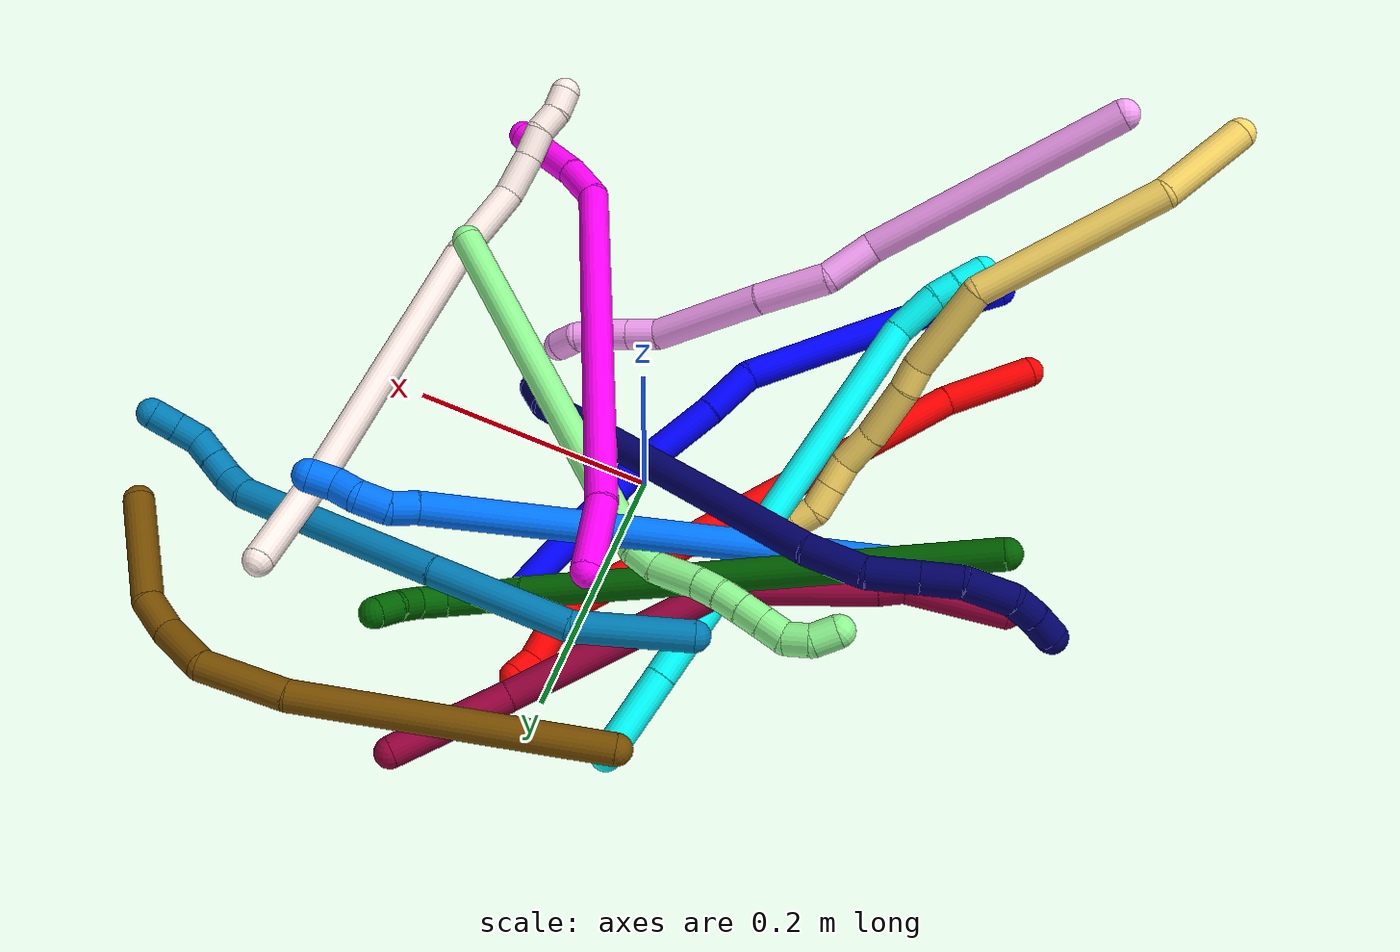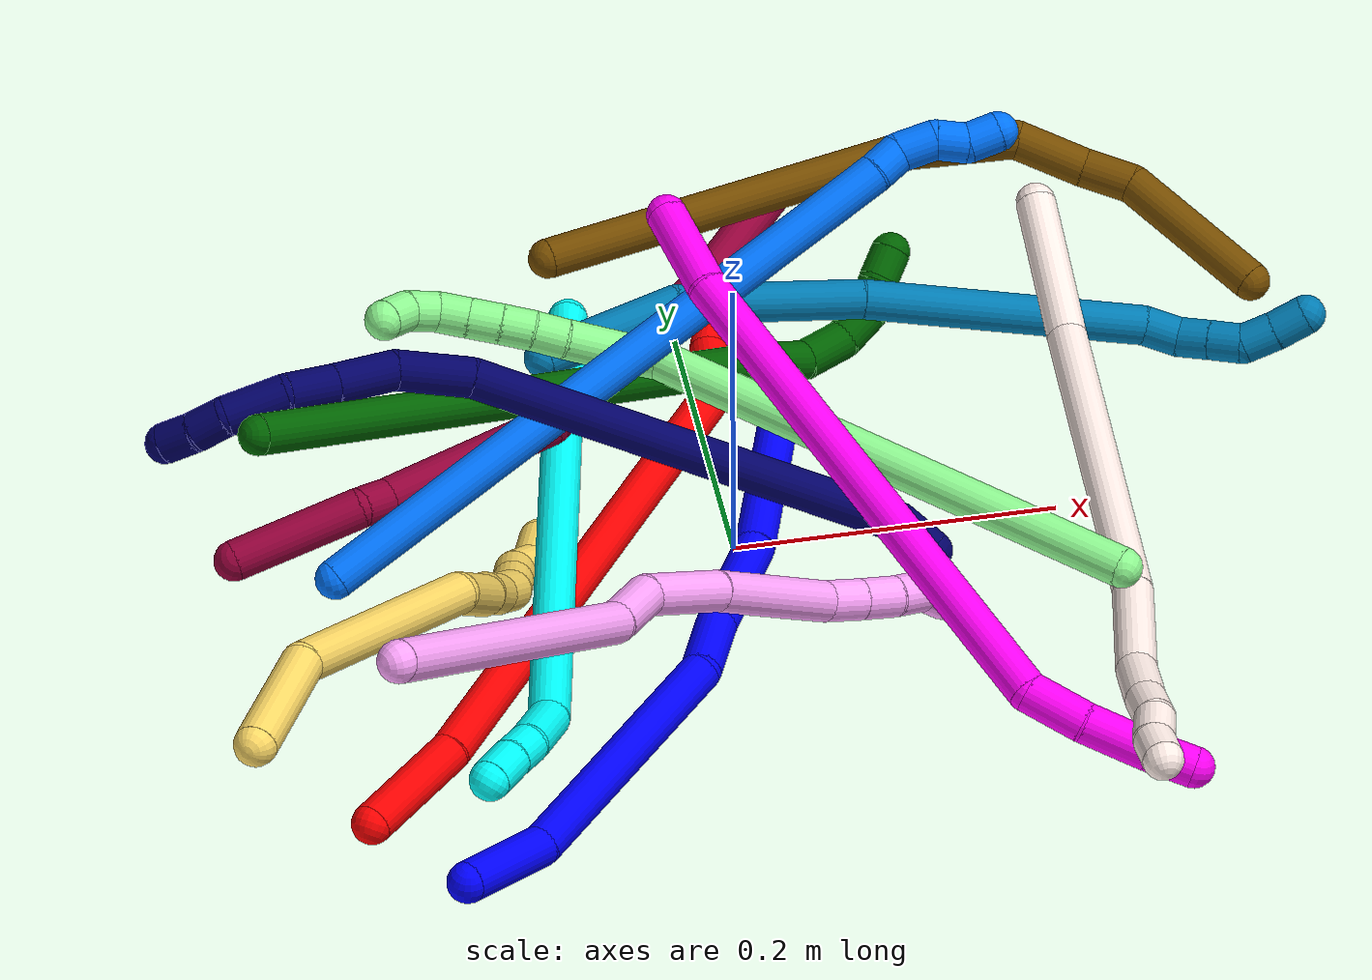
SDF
<sdf version="1.7">
 <world name="default">
  <plugin name="TubeGeneratorPlugin" filename="libtube_generator_plugin.so"/>
  <model name="photoneo_s_sensor">
   <static>1</static>
   <pose>0 0 2 1.57079 1.57079 3.14159</pose>
   <link name="link">
    <inertial><mass>0.1</mass></inertial>
    <sensor name="sensor" type="depth">
     <update_rate>30</update_rate>
     <camera>
      <horizontal_fov>1.22</horizontal_fov>
      <image><width>1920</width><height>1200</height><format>B8G8R8</format></image>
      <clip><near>0.1</near><far>4</far></clip>
      <depth_camera><output>points</output></depth_camera>
     </camera>
     <plugin name="camera_plugin" filename="libgazebo_ros_depth_camera.so">
      <baseline>0.2</baseline>
      <alwaysOn>1</alwaysOn>
      <updateRate>0.0</updateRate>
      <cameraName>camera_ir</cameraName>
      <imageTopicName>/camera/color/image_raw</imageTopicName>
      <cameraInfoTopicName>/camera/color/camera_info</cameraInfoTopicName>
      <depthImageTopicName>/camera/depth/image_raw</depthImageTopicName>
      <depthImageCameraInfoTopicName>/camera/depth/camera_info</depthImageCameraInfoTopicName>
      <pointCloudTopicName>/camera/depth/points</pointCloudTopicName>
      <frameName>fr_optical</frameName>
      <pointCloudCutoff>0.1</pointCloudCutoff>
      <pointCloudCutoffMax>2.0</pointCloudCutoffMax>
      <distortionK1>0</distortionK1>
      <distortionK2>0</distortionK2>
      <distortionK3>0</distortionK3>
      <distortionT1>0</distortionT1>
      <distortionT2>0</distortionT2>
      <CxPrime>0</CxPrime>
      <Cx>0</Cx>
      <Cy>0</Cy>
      <focalLength>0</focalLength>
      <hackBaseline>0</hackBaseline>
     </plugin>
    </sensor>
   </link>
  </model>
  <gravity>0 0 -9.8</gravity>
  <magnetic_field>6e-06 2.3e-05 -4.2e-05</magnetic_field>
  <atmosphere type="adiabatic"/>
  <physics name="default_physics" default="0" type="ode">
   <max_step_size>0.003</max_step_size>
   <real_time_factor>1</real_time_factor>
   <real_time_update_rate>1000</real_time_update_rate>
   <max_contacts>10000</max_contacts>
   <ode>
    <solver>
     <type>quick</type>
     <iters>100</iters>
     <sor>1.3</sor>
     <use_dynamic_moi_rescaling>0</use_dynamic_moi_rescaling>
    </solver>
    <constraints>
     <contact_max_correcting_vel>0</contact_max_correcting_vel>
     <contact_surface_layer>0.001</contact_surface_layer>
     <cfm>0</cfm>
     <erp>0.2</erp>
    </constraints>
   </ode>
  </physics>
  <scene><ambient>0.4 0.4 0.4 1</ambient><background>0.7 0.7 0.7 1</background><shadows>0</shadows></scene>
  <audio><device>default</device></audio>
  <spherical_coordinates>
   <surface_model>EARTH_WGS84</surface_model>
   <latitude_deg>0</latitude_deg>
   <longitude_deg>0</longitude_deg>
   <elevation>0</elevation>
   <heading_deg>0</heading_deg>
  </spherical_coordinates>
  <model name="bin">
   <static>1</static>
   <link name="bottom">
    <collision name="collision-bottom">
     <pose>0 0 -0.01 0 -0 0</pose>
     <geometry><box><size>0.8 0.6 0.02</size></box></geometry>
     <surface>
      <friction><ode><mu>100</mu><mu2>100</mu2></ode></friction>
      <contact><collide_bitmask>65535</collide_bitmask></contact>
     </surface>
    </collision>
   </link>
   <link name="west_wall">
    <collision name="collision-west_wall">
     <pose>-0.41 0 0.1 0 -0 0</pose>
     <geometry><box><size>0.02 0.6 0.2</size></box></geometry>
     <surface>
      <friction><ode><mu>100</mu><mu2>100</mu2></ode></friction>
      <contact><collide_bitmask>65535</collide_bitmask></contact>
     </surface>
    </collision>
   </link>
   <link name="east_wall">
    <collision name="collision-east_wall">
     <pose>0.41 0 0.1 0 -0 0</pose>
     <geometry><box><size>0.02 0.6 0.2</size></box></geometry>
     <surface>
      <friction><ode><mu>100</mu><mu2>100</mu2></ode></friction>
      <contact><collide_bitmask>65535</collide_bitmask></contact>
     </surface>
    </collision>
   </link>
   <link name="south_wall">
    <collision name="collision-south_wall">
     <pose>0 -0.31 0.1 0 -0 0</pose>
     <geometry><box><size>0.8 0.02 0.2</size></box></geometry>
     <surface>
      <friction><ode><mu>100</mu><mu2>100</mu2></ode></friction>
      <contact><collide_bitmask>65535</collide_bitmask></contact>
     </surface>
    </collision>
   </link>
   <link name="north_wall">
    <collision name="collision-north_wall">
     <pose>0 0.31 0.1 0 -0 0</pose>
     <geometry><box><size>0.8 0.02 0.2</size></box></geometry>
     <surface>
      <friction><ode><mu>100</mu><mu2>100</mu2></ode></friction>
      <contact><collide_bitmask>65535</collide_bitmask></contact>
     </surface>
    </collision>
   </link>
  </model>
  <model name="1">
   <static>0</static>
   <link name="1">
    <collision name="collision-cylinder-e_1_1_4">
     <pose>-0.0206 -0.069524 0.003262 1.52391 -0.28776 -0.274745</pose>
     <geometry><cylinder><radius>0.0125</radius><length>0.145169</length></cylinder></geometry>
     <surface>
      <friction><ode><mu>1.16</mu><mu2>1.16</mu2><slip1>0</slip1><slip2>0</slip2></ode></friction>
      <contact><ode><kp>1e+06</kp><kd>1</kd><max_vel>0</max_vel><min_depth>0.001</min_depth></ode></contact>
     </surface>
    </collision>
    <visual name="visual-cylinder-e_1_1_4">
     <pose>-0.0206 -0.069524 0.003262 1.52391 -0.28776 -0.274745</pose>
     <geometry><cylinder><radius>0.0125</radius><length>0.145169</length></cylinder></geometry>
     <material><ambient>0 0 1 1</ambient></material>
    </visual>
    <collision name="collision-cylinder-e_2_4_5">
     <pose>-0.059053 -0.174925 0.009896 1.47709 -0.459981 -0.420033</pose>
     <geometry><cylinder><radius>0.0125</radius><length>0.080432</length></cylinder></geometry>
     <surface>
      <friction><ode><mu>1.16</mu><mu2>1.16</mu2><slip1>0</slip1><slip2>0</slip2></ode></friction>
      <contact><ode><kp>1e+06</kp><kd>1</kd><max_vel>0</max_vel><min_depth>0.001</min_depth></ode></contact>
     </surface>
    </collision>
    <visual name="visual-cylinder-e_2_4_5">
     <pose>-0.059053 -0.174925 0.009896 1.47709 -0.459981 -0.420033</pose>
     <geometry><cylinder><radius>0.0125</radius><length>0.080432</length></cylinder></geometry>
     <material><ambient>0 0 1 1</ambient></material>
    </visual>
    <collision name="collision-cylinder-e_3_5_6">
     <pose>-0.085 -0.231479 0.014678 1.50268 -0.372326 -0.348301</pose>
     <geometry><cylinder><radius>0.0125</radius><length>0.044497</length></cylinder></geometry>
     <surface>
      <friction><ode><mu>1.16</mu><mu2>1.16</mu2><slip1>0</slip1><slip2>0</slip2></ode></friction>
      <contact><ode><kp>1e+06</kp><kd>1</kd><max_vel>0</max_vel><min_depth>0.001</min_depth></ode></contact>
     </surface>
    </collision>
    <visual name="visual-cylinder-e_3_5_6">
     <pose>-0.085 -0.231479 0.014678 1.50268 -0.372326 -0.348301</pose>
     <geometry><cylinder><radius>0.0125</radius><length>0.044497</length></cylinder></geometry>
     <material><ambient>0 0 1 1</ambient></material>
    </visual>
    <collision name="collision-cylinder-e_4_6_7">
     <pose>-0.149591 -0.31415 0.00971 1.67333 -0.736419 -0.808041</pose>
     <geometry><cylinder><radius>0.0125</radius><length>0.16824</length></cylinder></geometry>
     <surface>
      <friction><ode><mu>1.16</mu><mu2>1.16</mu2><slip1>0</slip1><slip2>0</slip2></ode></friction>
      <contact><ode><kp>1e+06</kp><kd>1</kd><max_vel>0</max_vel><min_depth>0.001</min_depth></ode></contact>
     </surface>
    </collision>
    <visual name="visual-cylinder-e_4_6_7">
     <pose>-0.149591 -0.31415 0.00971 1.67333 -0.736419 -0.808041</pose>
     <geometry><cylinder><radius>0.0125</radius><length>0.16824</length></cylinder></geometry>
     <material><ambient>0 0 1 1</ambient></material>
    </visual>
    <collision name="collision-cylinder-e_5_7_2">
     <pose>-0.230491 -0.394242 0.00859 1.28795 -0.913177 -0.706594</pose>
     <geometry><cylinder><radius>0.0125</radius><length>0.061663</length></cylinder></geometry>
     <surface>
      <friction><ode><mu>1.16</mu><mu2>1.16</mu2><slip1>0</slip1><slip2>0</slip2></ode></friction>
      <contact><ode><kp>1e+06</kp><kd>1</kd><max_vel>0</max_vel><min_depth>0.001</min_depth></ode></contact>
     </surface>
    </collision>
    <visual name="visual-cylinder-e_5_7_2">
     <pose>-0.230491 -0.394242 0.00859 1.28795 -0.913177 -0.706594</pose>
     <geometry><cylinder><radius>0.0125</radius><length>0.061663</length></cylinder></geometry>
     <material><ambient>0 0 1 1</ambient></material>
    </visual>
    <collision name="collision-sphere-2">
     <pose>-0.254892 -0.412338 0.013849 0 -0 0</pose>
     <geometry><sphere><radius>0.0125</radius></sphere></geometry>
     <surface>
      <friction><ode><mu>1.16</mu><mu2>1.16</mu2><slip1>0</slip1><slip2>0</slip2></ode></friction>
      <contact><ode><kp>1e+06</kp><kd>1</kd><max_vel>0</max_vel><min_depth>0.001</min_depth></ode></contact>
     </surface>
    </collision>
    <visual name="visual-sphere-2">
     <pose>-0.254892 -0.412338 0.013849 0 -0 0</pose>
     <geometry><sphere><radius>0.0125</radius></sphere></geometry>
     <material><ambient>0 0 1 1</ambient></material>
    </visual>
    <collision name="collision-sphere-7">
     <pose>-0.206089 -0.376145 0.00333 0 -0 0</pose>
     <geometry><sphere><radius>0.0125</radius></sphere></geometry>
     <surface>
      <friction><ode><mu>1.16</mu><mu2>1.16</mu2><slip1>0</slip1><slip2>0</slip2></ode></friction>
      <contact><ode><kp>1e+06</kp><kd>1</kd><max_vel>0</max_vel><min_depth>0.001</min_depth></ode></contact>
     </surface>
    </collision>
    <visual name="visual-sphere-7">
     <pose>-0.206089 -0.376145 0.00333 0 -0 0</pose>
     <geometry><sphere><radius>0.0125</radius></sphere></geometry>
     <material><ambient>0 0 1 1</ambient></material>
    </visual>
    <collision name="collision-sphere-6">
     <pose>-0.093093 -0.252155 0.016089 0 -0 0</pose>
     <geometry><sphere><radius>0.0125</radius></sphere></geometry>
     <surface>
      <friction><ode><mu>1.16</mu><mu2>1.16</mu2><slip1>0</slip1><slip2>0</slip2></ode></friction>
      <contact><ode><kp>1e+06</kp><kd>1</kd><max_vel>0</max_vel><min_depth>0.001</min_depth></ode></contact>
     </surface>
    </collision>
    <visual name="visual-sphere-6">
     <pose>-0.093093 -0.252155 0.016089 0 -0 0</pose>
     <geometry><sphere><radius>0.0125</radius></sphere></geometry>
     <material><ambient>0 0 1 1</ambient></material>
    </visual>
    <collision name="collision-sphere-5">
     <pose>-0.076906 -0.210803 0.013268 0 -0 0</pose>
     <geometry><sphere><radius>0.0125</radius></sphere></geometry>
     <surface>
      <friction><ode><mu>1.16</mu><mu2>1.16</mu2><slip1>0</slip1><slip2>0</slip2></ode></friction>
      <contact><ode><kp>1e+06</kp><kd>1</kd><max_vel>0</max_vel><min_depth>0.001</min_depth></ode></contact>
     </surface>
    </collision>
    <visual name="visual-sphere-5">
     <pose>-0.076906 -0.210803 0.013268 0 -0 0</pose>
     <geometry><sphere><radius>0.0125</radius></sphere></geometry>
     <material><ambient>0 0 1 1</ambient></material>
    </visual>
    <collision name="collision-sphere-1">
     <geometry><sphere><radius>0.0125</radius></sphere></geometry>
     <surface>
      <friction><ode><mu>1.16</mu><mu2>1.16</mu2><slip1>0</slip1><slip2>0</slip2></ode></friction>
      <contact><ode><kp>1e+06</kp><kd>1</kd><max_vel>0</max_vel><min_depth>0.001</min_depth></ode></contact>
     </surface>
    </collision>
    <visual name="visual-sphere-1">
     <geometry><sphere><radius>0.0125</radius></sphere></geometry>
     <material><ambient>0 0 1 1</ambient></material>
    </visual>
    <collision name="collision-sphere-4">
     <pose>-0.0412 -0.139047 0.006524 0 -0 0</pose>
     <geometry><sphere><radius>0.0125</radius></sphere></geometry>
     <surface>
      <friction><ode><mu>1.16</mu><mu2>1.16</mu2><slip1>0</slip1><slip2>0</slip2></ode></friction>
      <contact><ode><kp>1e+06</kp><kd>1</kd><max_vel>0</max_vel><min_depth>0.001</min_depth></ode></contact>
     </surface>
    </collision>
    <visual name="visual-sphere-4">
     <pose>-0.0412 -0.139047 0.006524 0 -0 0</pose>
     <geometry><sphere><radius>0.0125</radius></sphere></geometry>
     <material><ambient>0 0 1 1</ambient></material>
    </visual>
    <inertial>
     <pose>-0.101804 -0.223249 0.008172 0 -0 0</pose>
     <mass>0.5</mass>
     <inertia>
      <ixx>0.000171</ixx>
      <ixy>0</ixy>
      <ixz>0</ixz>
      <iyy>-0.000117</iyy>
      <iyz>0</iyz>
      <izz>0.000997</izz>
     </inertia>
    </inertial>
   </link>
   <pose>0.055939 0.132226 0.001002 0.049211 0.075123 -0.020394</pose>
  </model>
  <model name="2">
   <static>0</static>
   <link name="2">
    <collision name="collision-cylinder-e_1_1_4">
     <pose>0.006515 0.023853 -0.028383 -2.44269 0.173947 -0.46972</pose>
     <geometry><cylinder><radius>0.0125</radius><length>0.075287</length></cylinder></geometry>
     <surface>
      <friction><ode><mu>1.16</mu><mu2>1.16</mu2><slip1>0</slip1><slip2>0</slip2></ode></friction>
      <contact><ode><kp>1e+06</kp><kd>1</kd><max_vel>0</max_vel><min_depth>0.001</min_depth></ode></contact>
     </surface>
    </collision>
    <visual name="visual-cylinder-e_1_1_4">
     <pose>0.006515 0.023853 -0.028383 -2.44269 0.173947 -0.46972</pose>
     <geometry><cylinder><radius>0.0125</radius><length>0.075287</length></cylinder></geometry>
     <material><ambient>1 0 0 1</ambient></material>
    </visual>
    <collision name="collision-cylinder-e_2_4_5">
     <pose>0.06875 0.144123 -0.191368 -2.52001 0.324627 -0.942941</pose>
     <geometry><cylinder><radius>0.0125</radius><length>0.349391</length></cylinder></geometry>
     <surface>
      <friction><ode><mu>1.16</mu><mu2>1.16</mu2><slip1>0</slip1><slip2>0</slip2></ode></friction>
      <contact><ode><kp>1e+06</kp><kd>1</kd><max_vel>0</max_vel><min_depth>0.001</min_depth></ode></contact>
     </surface>
    </collision>
    <visual name="visual-cylinder-e_2_4_5">
     <pose>0.06875 0.144123 -0.191368 -2.52001 0.324627 -0.942941</pose>
     <geometry><cylinder><radius>0.0125</radius><length>0.349391</length></cylinder></geometry>
     <material><ambient>1 0 0 1</ambient></material>
    </visual>
    <collision name="collision-cylinder-e_3_5_6">
     <pose>0.134232 0.246781 -0.335251 -2.54947 0.717615 -1.77599</pose>
     <geometry><cylinder><radius>0.0125</radius><length>0.02969</length></cylinder></geometry>
     <surface>
      <friction><ode><mu>1.16</mu><mu2>1.16</mu2><slip1>0</slip1><slip2>0</slip2></ode></friction>
      <contact><ode><kp>1e+06</kp><kd>1</kd><max_vel>0</max_vel><min_depth>0.001</min_depth></ode></contact>
     </surface>
    </collision>
    <visual name="visual-cylinder-e_3_5_6">
     <pose>0.134232 0.246781 -0.335251 -2.54947 0.717615 -1.77599</pose>
     <geometry><cylinder><radius>0.0125</radius><length>0.02969</length></cylinder></geometry>
     <material><ambient>1 0 0 1</ambient></material>
    </visual>
    <collision name="collision-cylinder-e_4_6_7">
     <pose>0.15345 0.256245 -0.352414 -2.75365 0.83761 -2.31039</pose>
     <geometry><cylinder><radius>0.0125</radius><length>0.025451</length></cylinder></geometry>
     <surface>
      <friction><ode><mu>1.16</mu><mu2>1.16</mu2><slip1>0</slip1><slip2>0</slip2></ode></friction>
      <contact><ode><kp>1e+06</kp><kd>1</kd><max_vel>0</max_vel><min_depth>0.001</min_depth></ode></contact>
     </surface>
    </collision>
    <visual name="visual-cylinder-e_4_6_7">
     <pose>0.15345 0.256245 -0.352414 -2.75365 0.83761 -2.31039</pose>
     <geometry><cylinder><radius>0.0125</radius><length>0.025451</length></cylinder></geometry>
     <material><ambient>1 0 0 1</ambient></material>
    </visual>
    <collision name="collision-cylinder-e_5_7_2">
     <pose>0.167049 0.261847 -0.369185 -2.87982 0.423169 -2.04196</pose>
     <geometry><cylinder><radius>0.0125</radius><length>0.020181</length></cylinder></geometry>
     <surface>
      <friction><ode><mu>1.16</mu><mu2>1.16</mu2><slip1>0</slip1><slip2>0</slip2></ode></friction>
      <contact><ode><kp>1e+06</kp><kd>1</kd><max_vel>0</max_vel><min_depth>0.001</min_depth></ode></contact>
     </surface>
    </collision>
    <visual name="visual-cylinder-e_5_7_2">
     <pose>0.167049 0.261847 -0.369185 -2.87982 0.423169 -2.04196</pose>
     <geometry><cylinder><radius>0.0125</radius><length>0.020181</length></cylinder></geometry>
     <material><ambient>1 0 0 1</ambient></material>
    </visual>
    <collision name="collision-sphere-2">
     <pose>0.171193 0.264228 -0.378071 0 -0 0</pose>
     <geometry><sphere><radius>0.0125</radius></sphere></geometry>
     <surface>
      <friction><ode><mu>1.16</mu><mu2>1.16</mu2><slip1>0</slip1><slip2>0</slip2></ode></friction>
      <contact><ode><kp>1e+06</kp><kd>1</kd><max_vel>0</max_vel><min_depth>0.001</min_depth></ode></contact>
     </surface>
    </collision>
    <visual name="visual-sphere-2">
     <pose>0.171193 0.264228 -0.378071 0 -0 0</pose>
     <geometry><sphere><radius>0.0125</radius></sphere></geometry>
     <material><ambient>1 0 0 1</ambient></material>
    </visual>
    <collision name="collision-sphere-7">
     <pose>0.162905 0.259466 -0.360298 0 -0 0</pose>
     <geometry><sphere><radius>0.0125</radius></sphere></geometry>
     <surface>
      <friction><ode><mu>1.16</mu><mu2>1.16</mu2><slip1>0</slip1><slip2>0</slip2></ode></friction>
      <contact><ode><kp>1e+06</kp><kd>1</kd><max_vel>0</max_vel><min_depth>0.001</min_depth></ode></contact>
     </surface>
    </collision>
    <visual name="visual-sphere-7">
     <pose>0.162905 0.259466 -0.360298 0 -0 0</pose>
     <geometry><sphere><radius>0.0125</radius></sphere></geometry>
     <material><ambient>1 0 0 1</ambient></material>
    </visual>
    <collision name="collision-sphere-6">
     <pose>0.143994 0.253023 -0.34453 0 -0 0</pose>
     <geometry><sphere><radius>0.0125</radius></sphere></geometry>
     <surface>
      <friction><ode><mu>1.16</mu><mu2>1.16</mu2><slip1>0</slip1><slip2>0</slip2></ode></friction>
      <contact><ode><kp>1e+06</kp><kd>1</kd><max_vel>0</max_vel><min_depth>0.001</min_depth></ode></contact>
     </surface>
    </collision>
    <visual name="visual-sphere-6">
     <pose>0.143994 0.253023 -0.34453 0 -0 0</pose>
     <geometry><sphere><radius>0.0125</radius></sphere></geometry>
     <material><ambient>1 0 0 1</ambient></material>
    </visual>
    <collision name="collision-sphere-5">
     <pose>0.12447 0.240539 -0.325971 0 -0 0</pose>
     <geometry><sphere><radius>0.0125</radius></sphere></geometry>
     <surface>
      <friction><ode><mu>1.16</mu><mu2>1.16</mu2><slip1>0</slip1><slip2>0</slip2></ode></friction>
      <contact><ode><kp>1e+06</kp><kd>1</kd><max_vel>0</max_vel><min_depth>0.001</min_depth></ode></contact>
     </surface>
    </collision>
    <visual name="visual-sphere-5">
     <pose>0.12447 0.240539 -0.325971 0 -0 0</pose>
     <geometry><sphere><radius>0.0125</radius></sphere></geometry>
     <material><ambient>1 0 0 1</ambient></material>
    </visual>
    <collision name="collision-sphere-1">
     <geometry><sphere><radius>0.0125</radius></sphere></geometry>
     <surface>
      <friction><ode><mu>1.16</mu><mu2>1.16</mu2><slip1>0</slip1><slip2>0</slip2></ode></friction>
      <contact><ode><kp>1e+06</kp><kd>1</kd><max_vel>0</max_vel><min_depth>0.001</min_depth></ode></contact>
     </surface>
    </collision>
    <visual name="visual-sphere-1">
     <geometry><sphere><radius>0.0125</radius></sphere></geometry>
     <material><ambient>1 0 0 1</ambient></material>
    </visual>
    <collision name="collision-sphere-4">
     <pose>0.01303 0.047707 -0.056766 0 -0 0</pose>
     <geometry><sphere><radius>0.0125</radius></sphere></geometry>
     <surface>
      <friction><ode><mu>1.16</mu><mu2>1.16</mu2><slip1>0</slip1><slip2>0</slip2></ode></friction>
      <contact><ode><kp>1e+06</kp><kd>1</kd><max_vel>0</max_vel><min_depth>0.001</min_depth></ode></contact>
     </surface>
    </collision>
    <visual name="visual-sphere-4">
     <pose>0.01303 0.047707 -0.056766 0 -0 0</pose>
     <geometry><sphere><radius>0.0125</radius></sphere></geometry>
     <material><ambient>1 0 0 1</ambient></material>
    </visual>
    <inertial>
     <pose>0.071546 0.142568 -0.190745 0 -0 0</pose>
     <mass>0.5</mass>
     <inertia>
      <ixx>-0.000727</ixx>
      <ixy>0</ixy>
      <ixz>0</ixz>
      <iyy>-0.003925</iyy>
      <iyz>0</iyz>
      <izz>-0.003175</izz>
     </inertia>
    </inertial>
   </link>
   <pose>-0.253486 -0.213635 0.011497 -2.35184 0.402722 2.14841</pose>
  </model>
  <model name="3">
   <static>0</static>
   <link name="3">
    <collision name="collision-cylinder-e_1_1_4">
     <pose>0.007932 -0.029636 0.019639 0.985557 0.219496 0.118199</pose>
     <geometry><cylinder><radius>0.0125</radius><length>0.072854</length></cylinder></geometry>
     <surface>
      <friction><ode><mu>1.16</mu><mu2>1.16</mu2><slip1>0</slip1><slip2>0</slip2></ode></friction>
      <contact><ode><kp>1e+06</kp><kd>1</kd><max_vel>0</max_vel><min_depth>0.001</min_depth></ode></contact>
     </surface>
    </collision>
    <visual name="visual-cylinder-e_1_1_4">
     <pose>0.007932 -0.029636 0.019639 0.985557 0.219496 0.118199</pose>
     <geometry><cylinder><radius>0.0125</radius><length>0.072854</length></cylinder></geometry>
     <material><ambient>0.003922 1 0.996078 1</ambient></material>
    </visual>
    <collision name="collision-cylinder-e_2_4_5">
     <pose>0.050563 -0.198595 0.132927 0.978995 0.203837 0.108863</pose>
     <geometry><cylinder><radius>0.0125</radius><length>0.34284</length></cylinder></geometry>
     <surface>
      <friction><ode><mu>1.16</mu><mu2>1.16</mu2><slip1>0</slip1><slip2>0</slip2></ode></friction>
      <contact><ode><kp>1e+06</kp><kd>1</kd><max_vel>0</max_vel><min_depth>0.001</min_depth></ode></contact>
     </surface>
    </collision>
    <visual name="visual-cylinder-e_2_4_5">
     <pose>0.050563 -0.198595 0.132927 0.978995 0.203837 0.108863</pose>
     <geometry><cylinder><radius>0.0125</radius><length>0.34284</length></cylinder></geometry>
     <material><ambient>0.003922 1 0.996078 1</ambient></material>
    </visual>
    <collision name="collision-cylinder-e_3_5_6">
     <pose>0.096044 -0.351499 0.236182 0.955162 0.574976 0.303696</pose>
     <geometry><cylinder><radius>0.0125</radius><length>0.039647</length></cylinder></geometry>
     <surface>
      <friction><ode><mu>1.16</mu><mu2>1.16</mu2><slip1>0</slip1><slip2>0</slip2></ode></friction>
      <contact><ode><kp>1e+06</kp><kd>1</kd><max_vel>0</max_vel><min_depth>0.001</min_depth></ode></contact>
     </surface>
    </collision>
    <visual name="visual-cylinder-e_3_5_6">
     <pose>0.096044 -0.351499 0.236182 0.955162 0.574976 0.303696</pose>
     <geometry><cylinder><radius>0.0125</radius><length>0.039647</length></cylinder></geometry>
     <material><ambient>0.003922 1 0.996078 1</ambient></material>
    </visual>
    <collision name="collision-cylinder-e_4_6_7">
     <pose>0.11283 -0.370294 0.252123 0.688532 0.631909 0.233355</pose>
     <geometry><cylinder><radius>0.0125</radius><length>0.020332</length></cylinder></geometry>
     <surface>
      <friction><ode><mu>1.16</mu><mu2>1.16</mu2><slip1>0</slip1><slip2>0</slip2></ode></friction>
      <contact><ode><kp>1e+06</kp><kd>1</kd><max_vel>0</max_vel><min_depth>0.001</min_depth></ode></contact>
     </surface>
    </collision>
    <visual name="visual-cylinder-e_4_6_7">
     <pose>0.11283 -0.370294 0.252123 0.688532 0.631909 0.233355</pose>
     <geometry><cylinder><radius>0.0125</radius><length>0.020332</length></cylinder></geometry>
     <material><ambient>0.003922 1 0.996078 1</ambient></material>
    </visual>
    <collision name="collision-cylinder-e_5_7_2">
     <pose>0.125328 -0.381602 0.266741 0.634413 0.563167 0.189362</pose>
     <geometry><cylinder><radius>0.0125</radius><length>0.024326</length></cylinder></geometry>
     <surface>
      <friction><ode><mu>1.16</mu><mu2>1.16</mu2><slip1>0</slip1><slip2>0</slip2></ode></friction>
      <contact><ode><kp>1e+06</kp><kd>1</kd><max_vel>0</max_vel><min_depth>0.001</min_depth></ode></contact>
     </surface>
    </collision>
    <visual name="visual-cylinder-e_5_7_2">
     <pose>0.125328 -0.381602 0.266741 0.634413 0.563167 0.189362</pose>
     <geometry><cylinder><radius>0.0125</radius><length>0.024326</length></cylinder></geometry>
     <material><ambient>0.003922 1 0.996078 1</ambient></material>
    </visual>
    <collision name="collision-sphere-2">
     <pose>0.131822 -0.387697 0.275025 0 -0 0</pose>
     <geometry><sphere><radius>0.0125</radius></sphere></geometry>
     <surface>
      <friction><ode><mu>1.16</mu><mu2>1.16</mu2><slip1>0</slip1><slip2>0</slip2></ode></friction>
      <contact><ode><kp>1e+06</kp><kd>1</kd><max_vel>0</max_vel><min_depth>0.001</min_depth></ode></contact>
     </surface>
    </collision>
    <visual name="visual-sphere-2">
     <pose>0.131822 -0.387697 0.275025 0 -0 0</pose>
     <geometry><sphere><radius>0.0125</radius></sphere></geometry>
     <material><ambient>0.003922 1 0.996078 1</ambient></material>
    </visual>
    <collision name="collision-sphere-7">
     <pose>0.118835 -0.375506 0.258457 0 -0 0</pose>
     <geometry><sphere><radius>0.0125</radius></sphere></geometry>
     <surface>
      <friction><ode><mu>1.16</mu><mu2>1.16</mu2><slip1>0</slip1><slip2>0</slip2></ode></friction>
      <contact><ode><kp>1e+06</kp><kd>1</kd><max_vel>0</max_vel><min_depth>0.001</min_depth></ode></contact>
     </surface>
    </collision>
    <visual name="visual-sphere-7">
     <pose>0.118835 -0.375506 0.258457 0 -0 0</pose>
     <geometry><sphere><radius>0.0125</radius></sphere></geometry>
     <material><ambient>0.003922 1 0.996078 1</ambient></material>
    </visual>
    <collision name="collision-sphere-6">
     <pose>0.106825 -0.365081 0.245789 0 -0 0</pose>
     <geometry><sphere><radius>0.0125</radius></sphere></geometry>
     <surface>
      <friction><ode><mu>1.16</mu><mu2>1.16</mu2><slip1>0</slip1><slip2>0</slip2></ode></friction>
      <contact><ode><kp>1e+06</kp><kd>1</kd><max_vel>0</max_vel><min_depth>0.001</min_depth></ode></contact>
     </surface>
    </collision>
    <visual name="visual-sphere-6">
     <pose>0.106825 -0.365081 0.245789 0 -0 0</pose>
     <geometry><sphere><radius>0.0125</radius></sphere></geometry>
     <material><ambient>0.003922 1 0.996078 1</ambient></material>
    </visual>
    <collision name="collision-sphere-5">
     <pose>0.085264 -0.337917 0.226575 0 -0 0</pose>
     <geometry><sphere><radius>0.0125</radius></sphere></geometry>
     <surface>
      <friction><ode><mu>1.16</mu><mu2>1.16</mu2><slip1>0</slip1><slip2>0</slip2></ode></friction>
      <contact><ode><kp>1e+06</kp><kd>1</kd><max_vel>0</max_vel><min_depth>0.001</min_depth></ode></contact>
     </surface>
    </collision>
    <visual name="visual-sphere-5">
     <pose>0.085264 -0.337917 0.226575 0 -0 0</pose>
     <geometry><sphere><radius>0.0125</radius></sphere></geometry>
     <material><ambient>0.003922 1 0.996078 1</ambient></material>
    </visual>
    <collision name="collision-sphere-1">
     <geometry><sphere><radius>0.0125</radius></sphere></geometry>
     <surface>
      <friction><ode><mu>1.16</mu><mu2>1.16</mu2><slip1>0</slip1><slip2>0</slip2></ode></friction>
      <contact><ode><kp>1e+06</kp><kd>1</kd><max_vel>0</max_vel><min_depth>0.001</min_depth></ode></contact>
     </surface>
    </collision>
    <visual name="visual-sphere-1">
     <geometry><sphere><radius>0.0125</radius></sphere></geometry>
     <material><ambient>0.003922 1 0.996078 1</ambient></material>
    </visual>
    <collision name="collision-sphere-4">
     <pose>0.015863 -0.059272 0.039279 0 -0 0</pose>
     <geometry><sphere><radius>0.0125</radius></sphere></geometry>
     <surface>
      <friction><ode><mu>1.16</mu><mu2>1.16</mu2><slip1>0</slip1><slip2>0</slip2></ode></friction>
      <contact><ode><kp>1e+06</kp><kd>1</kd><max_vel>0</max_vel><min_depth>0.001</min_depth></ode></contact>
     </surface>
    </collision>
    <visual name="visual-sphere-4">
     <pose>0.015863 -0.059272 0.039279 0 -0 0</pose>
     <geometry><sphere><radius>0.0125</radius></sphere></geometry>
     <material><ambient>0.003922 1 0.996078 1</ambient></material>
    </visual>
    <inertial>
     <pose>0.054127 -0.201987 0.135965 0 -0 0</pose>
     <mass>0.5</mass>
     <inertia><ixx>0.0037</ixx><ixy>0</ixy><ixz>0</ixz><iyy>0.002294</iyy><iyz>0</iyz><izz>0.002101</izz></inertia>
    </inertial>
   </link>
   <pose>-0.064232 0.220074 0.012425 -2.62375 -0.777927 -3.13736</pose>
  </model>
  <model name="4">
   <static>0</static>
   <link name="4">
    <collision name="collision-cylinder-e_1_1_4">
     <pose>0.045437 0.013384 -0.095349 -3.00214 0.440927 -2.53739</pose>
     <geometry><cylinder><radius>0.0125</radius><length>0.212933</length></cylinder></geometry>
     <surface>
      <friction><ode><mu>1.16</mu><mu2>1.16</mu2><slip1>0</slip1><slip2>0</slip2></ode></friction>
      <contact><ode><kp>1e+06</kp><kd>1</kd><max_vel>0</max_vel><min_depth>0.001</min_depth></ode></contact>
     </surface>
    </collision>
    <visual name="visual-cylinder-e_1_1_4">
     <pose>0.045437 0.013384 -0.095349 -3.00214 0.440927 -2.53739</pose>
     <geometry><cylinder><radius>0.0125</radius><length>0.212933</length></cylinder></geometry>
     <material><ambient>1 0.65098 0.996078 1</ambient></material>
    </visual>
    <collision name="collision-cylinder-e_2_4_5">
     <pose>0.100914 0.022882 -0.208376 2.92527 0.506405 2.34694</pose>
     <geometry><cylinder><radius>0.0125</radius><length>0.041397</length></cylinder></geometry>
     <surface>
      <friction><ode><mu>1.16</mu><mu2>1.16</mu2><slip1>0</slip1><slip2>0</slip2></ode></friction>
      <contact><ode><kp>1e+06</kp><kd>1</kd><max_vel>0</max_vel><min_depth>0.001</min_depth></ode></contact>
     </surface>
    </collision>
    <visual name="visual-cylinder-e_2_4_5">
     <pose>0.100914 0.022882 -0.208376 2.92527 0.506405 2.34694</pose>
     <geometry><cylinder><radius>0.0125</radius><length>0.041397</length></cylinder></geometry>
     <material><ambient>1 0.65098 0.996078 1</ambient></material>
    </visual>
    <collision name="collision-cylinder-e_3_5_6">
     <pose>0.118691 0.025222 -0.253793 -2.92082 0.26572 -1.75685</pose>
     <geometry><cylinder><radius>0.0125</radius><length>0.058924</length></cylinder></geometry>
     <surface>
      <friction><ode><mu>1.16</mu><mu2>1.16</mu2><slip1>0</slip1><slip2>0</slip2></ode></friction>
      <contact><ode><kp>1e+06</kp><kd>1</kd><max_vel>0</max_vel><min_depth>0.001</min_depth></ode></contact>
     </surface>
    </collision>
    <visual name="visual-cylinder-e_3_5_6">
     <pose>0.118691 0.025222 -0.253793 -2.92082 0.26572 -1.75685</pose>
     <geometry><cylinder><radius>0.0125</radius><length>0.058924</length></cylinder></geometry>
     <material><ambient>1 0.65098 0.996078 1</ambient></material>
    </visual>
    <collision name="collision-cylinder-e_4_6_7">
     <pose>0.141005 0.045978 -0.324525 -2.81568 0.310809 -1.52255</pose>
     <geometry><cylinder><radius>0.0125</radius><length>0.095332</length></cylinder></geometry>
     <surface>
      <friction><ode><mu>1.16</mu><mu2>1.16</mu2><slip1>0</slip1><slip2>0</slip2></ode></friction>
      <contact><ode><kp>1e+06</kp><kd>1</kd><max_vel>0</max_vel><min_depth>0.001</min_depth></ode></contact>
     </surface>
    </collision>
    <visual name="visual-cylinder-e_4_6_7">
     <pose>0.141005 0.045978 -0.324525 -2.81568 0.310809 -1.52255</pose>
     <geometry><cylinder><radius>0.0125</radius><length>0.095332</length></cylinder></geometry>
     <material><ambient>1 0.65098 0.996078 1</ambient></material>
    </visual>
    <collision name="collision-cylinder-e_5_7_8">
     <pose>0.155337 0.063421 -0.379714 -2.90713 -0.019639 0.16638</pose>
     <geometry><cylinder><radius>0.0125</radius><length>0.025084</length></cylinder></geometry>
     <surface>
      <friction><ode><mu>1.16</mu><mu2>1.16</mu2><slip1>0</slip1><slip2>0</slip2></ode></friction>
      <contact><ode><kp>1e+06</kp><kd>1</kd><max_vel>0</max_vel><min_depth>0.001</min_depth></ode></contact>
     </surface>
    </collision>
    <visual name="visual-cylinder-e_5_7_8">
     <pose>0.155337 0.063421 -0.379714 -2.90713 -0.019639 0.16638</pose>
     <geometry><cylinder><radius>0.0125</radius><length>0.025084</length></cylinder></geometry>
     <material><ambient>1 0.65098 0.996078 1</ambient></material>
    </visual>
    <collision name="collision-cylinder-e_6_8_9">
     <pose>0.154883 0.068826 -0.403776 -2.93461 -0.017125 0.164515</pose>
     <geometry><cylinder><radius>0.0125</radius><length>0.024252</length></cylinder></geometry>
     <surface>
      <friction><ode><mu>1.16</mu><mu2>1.16</mu2><slip1>0</slip1><slip2>0</slip2></ode></friction>
      <contact><ode><kp>1e+06</kp><kd>1</kd><max_vel>0</max_vel><min_depth>0.001</min_depth></ode></contact>
     </surface>
    </collision>
    <visual name="visual-cylinder-e_6_8_9">
     <pose>0.154883 0.068826 -0.403776 -2.93461 -0.017125 0.164515</pose>
     <geometry><cylinder><radius>0.0125</radius><length>0.024252</length></cylinder></geometry>
     <material><ambient>1 0.65098 0.996078 1</ambient></material>
    </visual>
    <collision name="collision-cylinder-e_7_9_10">
     <pose>0.155421 0.072535 -0.426071 -3.02542 0.070931 -1.09564</pose>
     <geometry><cylinder><radius>0.0125</radius><length>0.021053</length></cylinder></geometry>
     <surface>
      <friction><ode><mu>1.16</mu><mu2>1.16</mu2><slip1>0</slip1><slip2>0</slip2></ode></friction>
      <contact><ode><kp>1e+06</kp><kd>1</kd><max_vel>0</max_vel><min_depth>0.001</min_depth></ode></contact>
     </surface>
    </collision>
    <visual name="visual-cylinder-e_7_9_10">
     <pose>0.155421 0.072535 -0.426071 -3.02542 0.070931 -1.09564</pose>
     <geometry><cylinder><radius>0.0125</radius><length>0.021053</length></cylinder></geometry>
     <material><ambient>1 0.65098 0.996078 1</ambient></material>
    </visual>
    <collision name="collision-cylinder-e_8_10_2">
     <pose>0.160091 0.078551 -0.444991 -2.62708 0.382474 -1.26883</pose>
     <geometry><cylinder><radius>0.0125</radius><length>0.021025</length></cylinder></geometry>
     <surface>
      <friction><ode><mu>1.16</mu><mu2>1.16</mu2><slip1>0</slip1><slip2>0</slip2></ode></friction>
      <contact><ode><kp>1e+06</kp><kd>1</kd><max_vel>0</max_vel><min_depth>0.001</min_depth></ode></contact>
     </surface>
    </collision>
    <visual name="visual-cylinder-e_8_10_2">
     <pose>0.160091 0.078551 -0.444991 -2.62708 0.382474 -1.26883</pose>
     <geometry><cylinder><radius>0.0125</radius><length>0.021025</length></cylinder></geometry>
     <material><ambient>1 0.65098 0.996078 1</ambient></material>
    </visual>
    <collision name="collision-sphere-2">
     <pose>0.164014 0.083351 -0.453481 0 -0 0</pose>
     <geometry><sphere><radius>0.0125</radius></sphere></geometry>
     <surface>
      <friction><ode><mu>1.16</mu><mu2>1.16</mu2><slip1>0</slip1><slip2>0</slip2></ode></friction>
      <contact><ode><kp>1e+06</kp><kd>1</kd><max_vel>0</max_vel><min_depth>0.001</min_depth></ode></contact>
     </surface>
    </collision>
    <visual name="visual-sphere-2">
     <pose>0.164014 0.083351 -0.453481 0 -0 0</pose>
     <geometry><sphere><radius>0.0125</radius></sphere></geometry>
     <material><ambient>1 0.65098 0.996078 1</ambient></material>
    </visual>
    <collision name="collision-sphere-10">
     <pose>0.156167 0.073752 -0.4365 0 -0 0</pose>
     <geometry><sphere><radius>0.0125</radius></sphere></geometry>
     <surface>
      <friction><ode><mu>1.16</mu><mu2>1.16</mu2><slip1>0</slip1><slip2>0</slip2></ode></friction>
      <contact><ode><kp>1e+06</kp><kd>1</kd><max_vel>0</max_vel><min_depth>0.001</min_depth></ode></contact>
     </surface>
    </collision>
    <visual name="visual-sphere-10">
     <pose>0.156167 0.073752 -0.4365 0 -0 0</pose>
     <geometry><sphere><radius>0.0125</radius></sphere></geometry>
     <material><ambient>1 0.65098 0.996078 1</ambient></material>
    </visual>
    <collision name="collision-sphere-9">
     <pose>0.154675 0.071318 -0.415642 0 -0 0</pose>
     <geometry><sphere><radius>0.0125</radius></sphere></geometry>
     <surface>
      <friction><ode><mu>1.16</mu><mu2>1.16</mu2><slip1>0</slip1><slip2>0</slip2></ode></friction>
      <contact><ode><kp>1e+06</kp><kd>1</kd><max_vel>0</max_vel><min_depth>0.001</min_depth></ode></contact>
     </surface>
    </collision>
    <visual name="visual-sphere-9">
     <pose>0.154675 0.071318 -0.415642 0 -0 0</pose>
     <geometry><sphere><radius>0.0125</radius></sphere></geometry>
     <material><ambient>1 0.65098 0.996078 1</ambient></material>
    </visual>
    <collision name="collision-sphere-4">
     <pose>0.090875 0.026767 -0.190698 0 -0 0</pose>
     <geometry><sphere><radius>0.0125</radius></sphere></geometry>
     <surface>
      <friction><ode><mu>1.16</mu><mu2>1.16</mu2><slip1>0</slip1><slip2>0</slip2></ode></friction>
      <contact><ode><kp>1e+06</kp><kd>1</kd><max_vel>0</max_vel><min_depth>0.001</min_depth></ode></contact>
     </surface>
    </collision>
    <visual name="visual-sphere-4">
     <pose>0.090875 0.026767 -0.190698 0 -0 0</pose>
     <geometry><sphere><radius>0.0125</radius></sphere></geometry>
     <material><ambient>1 0.65098 0.996078 1</ambient></material>
    </visual>
    <collision name="collision-sphere-1">
     <geometry><sphere><radius>0.0125</radius></sphere></geometry>
     <surface>
      <friction><ode><mu>1.16</mu><mu2>1.16</mu2><slip1>0</slip1><slip2>0</slip2></ode></friction>
      <contact><ode><kp>1e+06</kp><kd>1</kd><max_vel>0</max_vel><min_depth>0.001</min_depth></ode></contact>
     </surface>
    </collision>
    <visual name="visual-sphere-1">
     <geometry><sphere><radius>0.0125</radius></sphere></geometry>
     <material><ambient>1 0.65098 0.996078 1</ambient></material>
    </visual>
    <collision name="collision-sphere-8">
     <pose>0.15509 0.066334 -0.391911 0 -0 0</pose>
     <geometry><sphere><radius>0.0125</radius></sphere></geometry>
     <surface>
      <friction><ode><mu>1.16</mu><mu2>1.16</mu2><slip1>0</slip1><slip2>0</slip2></ode></friction>
      <contact><ode><kp>1e+06</kp><kd>1</kd><max_vel>0</max_vel><min_depth>0.001</min_depth></ode></contact>
     </surface>
    </collision>
    <visual name="visual-sphere-8">
     <pose>0.15509 0.066334 -0.391911 0 -0 0</pose>
     <geometry><sphere><radius>0.0125</radius></sphere></geometry>
     <material><ambient>1 0.65098 0.996078 1</ambient></material>
    </visual>
    <collision name="collision-sphere-5">
     <pose>0.110954 0.018997 -0.226055 0 -0 0</pose>
     <geometry><sphere><radius>0.0125</radius></sphere></geometry>
     <surface>
      <friction><ode><mu>1.16</mu><mu2>1.16</mu2><slip1>0</slip1><slip2>0</slip2></ode></friction>
      <contact><ode><kp>1e+06</kp><kd>1</kd><max_vel>0</max_vel><min_depth>0.001</min_depth></ode></contact>
     </surface>
    </collision>
    <visual name="visual-sphere-5">
     <pose>0.110954 0.018997 -0.226055 0 -0 0</pose>
     <geometry><sphere><radius>0.0125</radius></sphere></geometry>
     <material><ambient>1 0.65098 0.996078 1</ambient></material>
    </visual>
    <collision name="collision-sphere-6">
     <pose>0.126428 0.031448 -0.281531 0 -0 0</pose>
     <geometry><sphere><radius>0.0125</radius></sphere></geometry>
     <surface>
      <friction><ode><mu>1.16</mu><mu2>1.16</mu2><slip1>0</slip1><slip2>0</slip2></ode></friction>
      <contact><ode><kp>1e+06</kp><kd>1</kd><max_vel>0</max_vel><min_depth>0.001</min_depth></ode></contact>
     </surface>
    </collision>
    <visual name="visual-sphere-6">
     <pose>0.126428 0.031448 -0.281531 0 -0 0</pose>
     <geometry><sphere><radius>0.0125</radius></sphere></geometry>
     <material><ambient>1 0.65098 0.996078 1</ambient></material>
    </visual>
    <collision name="collision-sphere-7">
     <pose>0.155583 0.060508 -0.367518 0 -0 0</pose>
     <geometry><sphere><radius>0.0125</radius></sphere></geometry>
     <surface>
      <friction><ode><mu>1.16</mu><mu2>1.16</mu2><slip1>0</slip1><slip2>0</slip2></ode></friction>
      <contact><ode><kp>1e+06</kp><kd>1</kd><max_vel>0</max_vel><min_depth>0.001</min_depth></ode></contact>
     </surface>
    </collision>
    <visual name="visual-sphere-7">
     <pose>0.155583 0.060508 -0.367518 0 -0 0</pose>
     <geometry><sphere><radius>0.0125</radius></sphere></geometry>
     <material><ambient>1 0.65098 0.996078 1</ambient></material>
    </visual>
    <inertial>
     <pose>0.097159 0.03221 -0.224929 0 -0 0</pose>
     <mass>0.5</mass>
     <inertia>
      <ixx>-0.001097</ixx>
      <ixy>0</ixy>
      <ixz>0</ixz>
      <iyy>0.0002</iyy>
      <iyz>0</iyz>
      <izz>-0.000545</izz>
     </inertia>
    </inertial>
   </link>
   <pose>-0.248397 -0.324492 0.235269 -1.40811 0.666259 2.08623</pose>
  </model>
  <model name="5">
   <static>0</static>
   <link name="5">
    <collision name="collision-cylinder-e_1_1_4">
     <pose>0.007667 -0.004483 -0.037369 3.02219 0.200962 2.07129</pose>
     <geometry><cylinder><radius>0.0125</radius><length>0.07682</length></cylinder></geometry>
     <surface>
      <friction><ode><mu>1.16</mu><mu2>1.16</mu2><slip1>0</slip1><slip2>0</slip2></ode></friction>
      <contact><ode><kp>1e+06</kp><kd>1</kd><max_vel>0</max_vel><min_depth>0.001</min_depth></ode></contact>
     </surface>
    </collision>
    <visual name="visual-cylinder-e_1_1_4">
     <pose>0.007667 -0.004483 -0.037369 3.02219 0.200962 2.07129</pose>
     <geometry><cylinder><radius>0.0125</radius><length>0.07682</length></cylinder></geometry>
     <material><ambient>1 0.858824 0.4 1</ambient></material>
    </visual>
    <collision name="collision-cylinder-e_2_4_5">
     <pose>-0.00065 -0.015079 -0.150387 3.06097 -0.207574 -2.40271</pose>
     <geometry><cylinder><radius>0.0125</radius><length>0.155121</length></cylinder></geometry>
     <surface>
      <friction><ode><mu>1.16</mu><mu2>1.16</mu2><slip1>0</slip1><slip2>0</slip2></ode></friction>
      <contact><ode><kp>1e+06</kp><kd>1</kd><max_vel>0</max_vel><min_depth>0.001</min_depth></ode></contact>
     </surface>
    </collision>
    <visual name="visual-cylinder-e_2_4_5">
     <pose>-0.00065 -0.015079 -0.150387 3.06097 -0.207574 -2.40271</pose>
     <geometry><cylinder><radius>0.0125</radius><length>0.155121</length></cylinder></geometry>
     <material><ambient>1 0.858824 0.4 1</ambient></material>
    </visual>
    <collision name="collision-cylinder-e_3_5_6">
     <pose>-0.023666 -0.006339 -0.259559 -2.72453 -0.18949 0.844176</pose>
     <geometry><cylinder><radius>0.0125</radius><length>0.074668</length></cylinder></geometry>
     <surface>
      <friction><ode><mu>1.16</mu><mu2>1.16</mu2><slip1>0</slip1><slip2>0</slip2></ode></friction>
      <contact><ode><kp>1e+06</kp><kd>1</kd><max_vel>0</max_vel><min_depth>0.001</min_depth></ode></contact>
     </surface>
    </collision>
    <visual name="visual-cylinder-e_3_5_6">
     <pose>-0.023666 -0.006339 -0.259559 -2.72453 -0.18949 0.844176</pose>
     <geometry><cylinder><radius>0.0125</radius><length>0.074668</length></cylinder></geometry>
     <material><ambient>1 0.858824 0.4 1</ambient></material>
    </visual>
    <collision name="collision-cylinder-e_4_6_7">
     <pose>-0.030771 0.013709 -0.302647 -2.64404 -0.00663 0.026096</pose>
     <geometry><cylinder><radius>0.0125</radius><length>0.02177</length></cylinder></geometry>
     <surface>
      <friction><ode><mu>1.16</mu><mu2>1.16</mu2><slip1>0</slip1><slip2>0</slip2></ode></friction>
      <contact><ode><kp>1e+06</kp><kd>1</kd><max_vel>0</max_vel><min_depth>0.001</min_depth></ode></contact>
     </surface>
    </collision>
    <visual name="visual-cylinder-e_4_6_7">
     <pose>-0.030771 0.013709 -0.302647 -2.64404 -0.00663 0.026096</pose>
     <geometry><cylinder><radius>0.0125</radius><length>0.02177</length></cylinder></geometry>
     <material><ambient>1 0.858824 0.4 1</ambient></material>
    </visual>
    <collision name="collision-cylinder-e_5_7_8">
     <pose>-0.034491 0.028937 -0.332822 -2.68856 -0.157826 0.661043</pose>
     <geometry><cylinder><radius>0.0125</radius><length>0.046422</length></cylinder></geometry>
     <surface>
      <friction><ode><mu>1.16</mu><mu2>1.16</mu2><slip1>0</slip1><slip2>0</slip2></ode></friction>
      <contact><ode><kp>1e+06</kp><kd>1</kd><max_vel>0</max_vel><min_depth>0.001</min_depth></ode></contact>
     </surface>
    </collision>
    <visual name="visual-cylinder-e_5_7_8">
     <pose>-0.034491 0.028937 -0.332822 -2.68856 -0.157826 0.661043</pose>
     <geometry><cylinder><radius>0.0125</radius><length>0.046422</length></cylinder></geometry>
     <material><ambient>1 0.858824 0.4 1</ambient></material>
    </visual>
    <collision name="collision-cylinder-e_6_8_9">
     <pose>-0.040774 0.043304 -0.368025 -2.85289 -0.171381 1.06745</pose>
     <geometry><cylinder><radius>0.0125</radius><length>0.030899</length></cylinder></geometry>
     <surface>
      <friction><ode><mu>1.16</mu><mu2>1.16</mu2><slip1>0</slip1><slip2>0</slip2></ode></friction>
      <contact><ode><kp>1e+06</kp><kd>1</kd><max_vel>0</max_vel><min_depth>0.001</min_depth></ode></contact>
     </surface>
    </collision>
    <visual name="visual-cylinder-e_6_8_9">
     <pose>-0.040774 0.043304 -0.368025 -2.85289 -0.171381 1.06745</pose>
     <geometry><cylinder><radius>0.0125</radius><length>0.030899</length></cylinder></geometry>
     <material><ambient>1 0.858824 0.4 1</ambient></material>
    </visual>
    <collision name="collision-cylinder-e_7_9_10">
     <pose>-0.042065 0.05139 -0.392828 -2.78949 0.122891 -0.665937</pose>
     <geometry><cylinder><radius>0.0125</radius><length>0.021919</length></cylinder></geometry>
     <surface>
      <friction><ode><mu>1.16</mu><mu2>1.16</mu2><slip1>0</slip1><slip2>0</slip2></ode></friction>
      <contact><ode><kp>1e+06</kp><kd>1</kd><max_vel>0</max_vel><min_depth>0.001</min_depth></ode></contact>
     </surface>
    </collision>
    <visual name="visual-cylinder-e_7_9_10">
     <pose>-0.042065 0.05139 -0.392828 -2.78949 0.122891 -0.665937</pose>
     <geometry><cylinder><radius>0.0125</radius><length>0.021919</length></cylinder></geometry>
     <material><ambient>1 0.858824 0.4 1</ambient></material>
    </visual>
    <collision name="collision-cylinder-e_8_10_11">
     <pose>-0.039359 0.058975 -0.413685 -2.79597 0.119869 -0.662238</pose>
     <geometry><cylinder><radius>0.0125</radius><length>0.022798</length></cylinder></geometry>
     <surface>
      <friction><ode><mu>1.16</mu><mu2>1.16</mu2><slip1>0</slip1><slip2>0</slip2></ode></friction>
      <contact><ode><kp>1e+06</kp><kd>1</kd><max_vel>0</max_vel><min_depth>0.001</min_depth></ode></contact>
     </surface>
    </collision>
    <visual name="visual-cylinder-e_8_10_11">
     <pose>-0.039359 0.058975 -0.413685 -2.79597 0.119869 -0.662238</pose>
     <geometry><cylinder><radius>0.0125</radius><length>0.022798</length></cylinder></geometry>
     <material><ambient>1 0.858824 0.4 1</ambient></material>
    </visual>
    <collision name="collision-cylinder-e_9_11_12">
     <pose>-0.040233 0.062704 -0.434144 3.13093 -0.224186 -3.0469</pose>
     <geometry><cylinder><radius>0.0125</radius><length>0.020126</length></cylinder></geometry>
     <surface>
      <friction><ode><mu>1.16</mu><mu2>1.16</mu2><slip1>0</slip1><slip2>0</slip2></ode></friction>
      <contact><ode><kp>1e+06</kp><kd>1</kd><max_vel>0</max_vel><min_depth>0.001</min_depth></ode></contact>
     </surface>
    </collision>
    <visual name="visual-cylinder-e_9_11_12">
     <pose>-0.040233 0.062704 -0.434144 3.13093 -0.224186 -3.0469</pose>
     <geometry><cylinder><radius>0.0125</radius><length>0.020126</length></cylinder></geometry>
     <material><ambient>1 0.858824 0.4 1</ambient></material>
    </visual>
    <collision name="collision-cylinder-e_10_12_2">
     <pose>-0.038714 0.063567 -0.458163 -3.07358 0.257831 -2.62834</pose>
     <geometry><cylinder><radius>0.0125</radius><length>0.029457</length></cylinder></geometry>
     <surface>
      <friction><ode><mu>1.16</mu><mu2>1.16</mu2><slip1>0</slip1><slip2>0</slip2></ode></friction>
      <contact><ode><kp>1e+06</kp><kd>1</kd><max_vel>0</max_vel><min_depth>0.001</min_depth></ode></contact>
     </surface>
    </collision>
    <visual name="visual-cylinder-e_10_12_2">
     <pose>-0.038714 0.063567 -0.458163 -3.07358 0.257831 -2.62834</pose>
     <geometry><cylinder><radius>0.0125</radius><length>0.029457</length></cylinder></geometry>
     <material><ambient>1 0.858824 0.4 1</ambient></material>
    </visual>
    <collision name="collision-sphere-2">
     <pose>-0.034959 0.064535 -0.472372 0 -0 0</pose>
     <geometry><sphere><radius>0.0125</radius></sphere></geometry>
     <surface>
      <friction><ode><mu>1.16</mu><mu2>1.16</mu2><slip1>0</slip1><slip2>0</slip2></ode></friction>
      <contact><ode><kp>1e+06</kp><kd>1</kd><max_vel>0</max_vel><min_depth>0.001</min_depth></ode></contact>
     </surface>
    </collision>
    <visual name="visual-sphere-2">
     <pose>-0.034959 0.064535 -0.472372 0 -0 0</pose>
     <geometry><sphere><radius>0.0125</radius></sphere></geometry>
     <material><ambient>1 0.858824 0.4 1</ambient></material>
    </visual>
    <collision name="collision-sphere-12">
     <pose>-0.04247 0.0626 -0.443955 0 -0 0</pose>
     <geometry><sphere><radius>0.0125</radius></sphere></geometry>
     <surface>
      <friction><ode><mu>1.16</mu><mu2>1.16</mu2><slip1>0</slip1><slip2>0</slip2></ode></friction>
      <contact><ode><kp>1e+06</kp><kd>1</kd><max_vel>0</max_vel><min_depth>0.001</min_depth></ode></contact>
     </surface>
    </collision>
    <visual name="visual-sphere-12">
     <pose>-0.04247 0.0626 -0.443955 0 -0 0</pose>
     <geometry><sphere><radius>0.0125</radius></sphere></geometry>
     <material><ambient>1 0.858824 0.4 1</ambient></material>
    </visual>
    <collision name="collision-sphere-11">
     <pose>-0.037996 0.062809 -0.424333 0 -0 0</pose>
     <geometry><sphere><radius>0.0125</radius></sphere></geometry>
     <surface>
      <friction><ode><mu>1.16</mu><mu2>1.16</mu2><slip1>0</slip1><slip2>0</slip2></ode></friction>
      <contact><ode><kp>1e+06</kp><kd>1</kd><max_vel>0</max_vel><min_depth>0.001</min_depth></ode></contact>
     </surface>
    </collision>
    <visual name="visual-sphere-11">
     <pose>-0.037996 0.062809 -0.424333 0 -0 0</pose>
     <geometry><sphere><radius>0.0125</radius></sphere></geometry>
     <material><ambient>1 0.858824 0.4 1</ambient></material>
    </visual>
    <collision name="collision-sphere-10">
     <pose>-0.040722 0.055141 -0.403037 0 -0 0</pose>
     <geometry><sphere><radius>0.0125</radius></sphere></geometry>
     <surface>
      <friction><ode><mu>1.16</mu><mu2>1.16</mu2><slip1>0</slip1><slip2>0</slip2></ode></friction>
      <contact><ode><kp>1e+06</kp><kd>1</kd><max_vel>0</max_vel><min_depth>0.001</min_depth></ode></contact>
     </surface>
    </collision>
    <visual name="visual-sphere-10">
     <pose>-0.040722 0.055141 -0.403037 0 -0 0</pose>
     <geometry><sphere><radius>0.0125</radius></sphere></geometry>
     <material><ambient>1 0.858824 0.4 1</ambient></material>
    </visual>
    <collision name="collision-sphere-9">
     <pose>-0.043409 0.047639 -0.382618 0 -0 0</pose>
     <geometry><sphere><radius>0.0125</radius></sphere></geometry>
     <surface>
      <friction><ode><mu>1.16</mu><mu2>1.16</mu2><slip1>0</slip1><slip2>0</slip2></ode></friction>
      <contact><ode><kp>1e+06</kp><kd>1</kd><max_vel>0</max_vel><min_depth>0.001</min_depth></ode></contact>
     </surface>
    </collision>
    <visual name="visual-sphere-9">
     <pose>-0.043409 0.047639 -0.382618 0 -0 0</pose>
     <geometry><sphere><radius>0.0125</radius></sphere></geometry>
     <material><ambient>1 0.858824 0.4 1</ambient></material>
    </visual>
    <collision name="collision-sphere-4">
     <pose>0.015334 -0.008967 -0.074738 0 -0 0</pose>
     <geometry><sphere><radius>0.0125</radius></sphere></geometry>
     <surface>
      <friction><ode><mu>1.16</mu><mu2>1.16</mu2><slip1>0</slip1><slip2>0</slip2></ode></friction>
      <contact><ode><kp>1e+06</kp><kd>1</kd><max_vel>0</max_vel><min_depth>0.001</min_depth></ode></contact>
     </surface>
    </collision>
    <visual name="visual-sphere-4">
     <pose>0.015334 -0.008967 -0.074738 0 -0 0</pose>
     <geometry><sphere><radius>0.0125</radius></sphere></geometry>
     <material><ambient>1 0.858824 0.4 1</ambient></material>
    </visual>
    <collision name="collision-sphere-1">
     <geometry><sphere><radius>0.0125</radius></sphere></geometry>
     <surface>
      <friction><ode><mu>1.16</mu><mu2>1.16</mu2><slip1>0</slip1><slip2>0</slip2></ode></friction>
      <contact><ode><kp>1e+06</kp><kd>1</kd><max_vel>0</max_vel><min_depth>0.001</min_depth></ode></contact>
     </surface>
    </collision>
    <visual name="visual-sphere-1">
     <geometry><sphere><radius>0.0125</radius></sphere></geometry>
     <material><ambient>1 0.858824 0.4 1</ambient></material>
    </visual>
    <collision name="collision-sphere-8">
     <pose>-0.038139 0.03897 -0.353432 0 -0 0</pose>
     <geometry><sphere><radius>0.0125</radius></sphere></geometry>
     <surface>
      <friction><ode><mu>1.16</mu><mu2>1.16</mu2><slip1>0</slip1><slip2>0</slip2></ode></friction>
      <contact><ode><kp>1e+06</kp><kd>1</kd><max_vel>0</max_vel><min_depth>0.001</min_depth></ode></contact>
     </surface>
    </collision>
    <visual name="visual-sphere-8">
     <pose>-0.038139 0.03897 -0.353432 0 -0 0</pose>
     <geometry><sphere><radius>0.0125</radius></sphere></geometry>
     <material><ambient>1 0.858824 0.4 1</ambient></material>
    </visual>
    <collision name="collision-sphere-5">
     <pose>-0.016634 -0.021191 -0.226036 0 -0 0</pose>
     <geometry><sphere><radius>0.0125</radius></sphere></geometry>
     <surface>
      <friction><ode><mu>1.16</mu><mu2>1.16</mu2><slip1>0</slip1><slip2>0</slip2></ode></friction>
      <contact><ode><kp>1e+06</kp><kd>1</kd><max_vel>0</max_vel><min_depth>0.001</min_depth></ode></contact>
     </surface>
    </collision>
    <visual name="visual-sphere-5">
     <pose>-0.016634 -0.021191 -0.226036 0 -0 0</pose>
     <geometry><sphere><radius>0.0125</radius></sphere></geometry>
     <material><ambient>1 0.858824 0.4 1</ambient></material>
    </visual>
    <collision name="collision-sphere-6">
     <pose>-0.030698 0.008514 -0.293082 0 -0 0</pose>
     <geometry><sphere><radius>0.0125</radius></sphere></geometry>
     <surface>
      <friction><ode><mu>1.16</mu><mu2>1.16</mu2><slip1>0</slip1><slip2>0</slip2></ode></friction>
      <contact><ode><kp>1e+06</kp><kd>1</kd><max_vel>0</max_vel><min_depth>0.001</min_depth></ode></contact>
     </surface>
    </collision>
    <visual name="visual-sphere-6">
     <pose>-0.030698 0.008514 -0.293082 0 -0 0</pose>
     <geometry><sphere><radius>0.0125</radius></sphere></geometry>
     <material><ambient>1 0.858824 0.4 1</ambient></material>
    </visual>
    <collision name="collision-sphere-7">
     <pose>-0.030843 0.018904 -0.312212 0 -0 0</pose>
     <geometry><sphere><radius>0.0125</radius></sphere></geometry>
     <surface>
      <friction><ode><mu>1.16</mu><mu2>1.16</mu2><slip1>0</slip1><slip2>0</slip2></ode></friction>
      <contact><ode><kp>1e+06</kp><kd>1</kd><max_vel>0</max_vel><min_depth>0.001</min_depth></ode></contact>
     </surface>
    </collision>
    <visual name="visual-sphere-7">
     <pose>-0.030843 0.018904 -0.312212 0 -0 0</pose>
     <geometry><sphere><radius>0.0125</radius></sphere></geometry>
     <material><ambient>1 0.858824 0.4 1</ambient></material>
    </visual>
    <inertial>
     <pose>-0.017159 0.010857 -0.238531 0 -0 0</pose>
     <mass>0.5</mass>
     <inertia>
      <ixx>-0.000358</ixx>
      <ixy>0</ixy>
      <ixz>0</ixz>
      <iyy>9.3e-05</iyy>
      <iyz>0</iyz>
      <izz>3.6e-05</izz>
     </inertia>
    </inertial>
   </link>
   <pose>-0.333377 -0.356291 0.216054 -1.19755 -0.663504 2.34422</pose>
  </model>
  <model name="6">
   <static>0</static>
   <link name="6">
    <collision name="collision-cylinder-e_1_1_4">
     <pose>0.026394 -0.002763 -0.183295 3.12652 0.142997 2.93194</pose>
     <geometry><cylinder><radius>0.0125</radius><length>0.370412</length></cylinder></geometry>
     <surface>
      <friction><ode><mu>1.16</mu><mu2>1.16</mu2><slip1>0</slip1><slip2>0</slip2></ode></friction>
      <contact><ode><kp>1e+06</kp><kd>1</kd><max_vel>0</max_vel><min_depth>0.001</min_depth></ode></contact>
     </surface>
    </collision>
    <visual name="visual-cylinder-e_1_1_4">
     <pose>0.026394 -0.002763 -0.183295 3.12652 0.142997 2.93194</pose>
     <geometry><cylinder><radius>0.0125</radius><length>0.370412</length></cylinder></geometry>
     <material><ambient>0 0.392157 0.003922 1</ambient></material>
    </visual>
    <collision name="collision-cylinder-e_2_4_5">
     <pose>0.053124 -0.005715 -0.382797 3.12984 0.020756 2.11151</pose>
     <geometry><cylinder><radius>0.0125</radius><length>0.032424</length></cylinder></geometry>
     <surface>
      <friction><ode><mu>1.16</mu><mu2>1.16</mu2><slip1>0</slip1><slip2>0</slip2></ode></friction>
      <contact><ode><kp>1e+06</kp><kd>1</kd><max_vel>0</max_vel><min_depth>0.001</min_depth></ode></contact>
     </surface>
    </collision>
    <visual name="visual-cylinder-e_2_4_5">
     <pose>0.053124 -0.005715 -0.382797 3.12984 0.020756 2.11151</pose>
     <geometry><cylinder><radius>0.0125</radius><length>0.032424</length></cylinder></geometry>
     <material><ambient>0 0.392157 0.003922 1</ambient></material>
    </visual>
    <collision name="collision-cylinder-e_3_5_6">
     <pose>0.060087 -0.003844 -0.413511 -3.00038 0.424737 -2.50772</pose>
     <geometry><cylinder><radius>0.0125</radius><length>0.032162</length></cylinder></geometry>
     <surface>
      <friction><ode><mu>1.16</mu><mu2>1.16</mu2><slip1>0</slip1><slip2>0</slip2></ode></friction>
      <contact><ode><kp>1e+06</kp><kd>1</kd><max_vel>0</max_vel><min_depth>0.001</min_depth></ode></contact>
     </surface>
    </collision>
    <visual name="visual-cylinder-e_3_5_6">
     <pose>0.060087 -0.003844 -0.413511 -3.00038 0.424737 -2.50772</pose>
     <geometry><cylinder><radius>0.0125</radius><length>0.032162</length></cylinder></geometry>
     <material><ambient>0 0.392157 0.003922 1</ambient></material>
    </visual>
    <collision name="collision-cylinder-e_4_6_7">
     <pose>0.074659 0.001249 -0.436288 -2.79038 0.733909 -2.27662</pose>
     <geometry><cylinder><radius>0.0125</radius><length>0.023724</length></cylinder></geometry>
     <surface>
      <friction><ode><mu>1.16</mu><mu2>1.16</mu2><slip1>0</slip1><slip2>0</slip2></ode></friction>
      <contact><ode><kp>1e+06</kp><kd>1</kd><max_vel>0</max_vel><min_depth>0.001</min_depth></ode></contact>
     </surface>
    </collision>
    <visual name="visual-cylinder-e_4_6_7">
     <pose>0.074659 0.001249 -0.436288 -2.79038 0.733909 -2.27662</pose>
     <geometry><cylinder><radius>0.0125</radius><length>0.023724</length></cylinder></geometry>
     <material><ambient>0 0.392157 0.003922 1</ambient></material>
    </visual>
    <collision name="collision-cylinder-e_5_7_8">
     <pose>0.091552 0.008993 -0.447433 -2.11838 1.01797 -1.56464</pose>
     <geometry><cylinder><radius>0.0125</radius><length>0.02103</length></cylinder></geometry>
     <surface>
      <friction><ode><mu>1.16</mu><mu2>1.16</mu2><slip1>0</slip1><slip2>0</slip2></ode></friction>
      <contact><ode><kp>1e+06</kp><kd>1</kd><max_vel>0</max_vel><min_depth>0.001</min_depth></ode></contact>
     </surface>
    </collision>
    <visual name="visual-cylinder-e_5_7_8">
     <pose>0.091552 0.008993 -0.447433 -2.11838 1.01797 -1.56464</pose>
     <geometry><cylinder><radius>0.0125</radius><length>0.02103</length></cylinder></geometry>
     <material><ambient>0 0.392157 0.003922 1</ambient></material>
    </visual>
    <collision name="collision-cylinder-e_6_8_2">
     <pose>0.1078 0.018766 -0.455169 -2.33636 0.805178 -1.57073</pose>
     <geometry><cylinder><radius>0.0125</radius><length>0.020248</length></cylinder></geometry>
     <surface>
      <friction><ode><mu>1.16</mu><mu2>1.16</mu2><slip1>0</slip1><slip2>0</slip2></ode></friction>
      <contact><ode><kp>1e+06</kp><kd>1</kd><max_vel>0</max_vel><min_depth>0.001</min_depth></ode></contact>
     </surface>
    </collision>
    <visual name="visual-cylinder-e_6_8_2">
     <pose>0.1078 0.018766 -0.455169 -2.33636 0.805178 -1.57073</pose>
     <geometry><cylinder><radius>0.0125</radius><length>0.020248</length></cylinder></geometry>
     <material><ambient>0 0.392157 0.003922 1</ambient></material>
    </visual>
    <collision name="collision-sphere-2">
     <pose>0.115099 0.023824 -0.460031 0 -0 0</pose>
     <geometry><sphere><radius>0.0125</radius></sphere></geometry>
     <surface>
      <friction><ode><mu>1.16</mu><mu2>1.16</mu2><slip1>0</slip1><slip2>0</slip2></ode></friction>
      <contact><ode><kp>1e+06</kp><kd>1</kd><max_vel>0</max_vel><min_depth>0.001</min_depth></ode></contact>
     </surface>
    </collision>
    <visual name="visual-sphere-2">
     <pose>0.115099 0.023824 -0.460031 0 -0 0</pose>
     <geometry><sphere><radius>0.0125</radius></sphere></geometry>
     <material><ambient>0 0.392157 0.003922 1</ambient></material>
    </visual>
    <collision name="collision-sphere-4">
     <pose>0.052787 -0.005525 -0.36659 0 -0 0</pose>
     <geometry><sphere><radius>0.0125</radius></sphere></geometry>
     <surface>
      <friction><ode><mu>1.16</mu><mu2>1.16</mu2><slip1>0</slip1><slip2>0</slip2></ode></friction>
      <contact><ode><kp>1e+06</kp><kd>1</kd><max_vel>0</max_vel><min_depth>0.001</min_depth></ode></contact>
     </surface>
    </collision>
    <visual name="visual-sphere-4">
     <pose>0.052787 -0.005525 -0.36659 0 -0 0</pose>
     <geometry><sphere><radius>0.0125</radius></sphere></geometry>
     <material><ambient>0 0.392157 0.003922 1</ambient></material>
    </visual>
    <collision name="collision-sphere-1">
     <geometry><sphere><radius>0.0125</radius></sphere></geometry>
     <surface>
      <friction><ode><mu>1.16</mu><mu2>1.16</mu2><slip1>0</slip1><slip2>0</slip2></ode></friction>
      <contact><ode><kp>1e+06</kp><kd>1</kd><max_vel>0</max_vel><min_depth>0.001</min_depth></ode></contact>
     </surface>
    </collision>
    <visual name="visual-sphere-1">
     <geometry><sphere><radius>0.0125</radius></sphere></geometry>
     <material><ambient>0 0.392157 0.003922 1</ambient></material>
    </visual>
    <collision name="collision-sphere-8">
     <pose>0.100501 0.013707 -0.450308 0 -0 0</pose>
     <geometry><sphere><radius>0.0125</radius></sphere></geometry>
     <surface>
      <friction><ode><mu>1.16</mu><mu2>1.16</mu2><slip1>0</slip1><slip2>0</slip2></ode></friction>
      <contact><ode><kp>1e+06</kp><kd>1</kd><max_vel>0</max_vel><min_depth>0.001</min_depth></ode></contact>
     </surface>
    </collision>
    <visual name="visual-sphere-8">
     <pose>0.100501 0.013707 -0.450308 0 -0 0</pose>
     <geometry><sphere><radius>0.0125</radius></sphere></geometry>
     <material><ambient>0 0.392157 0.003922 1</ambient></material>
    </visual>
    <collision name="collision-sphere-5">
     <pose>0.05346 -0.005906 -0.399005 0 -0 0</pose>
     <geometry><sphere><radius>0.0125</radius></sphere></geometry>
     <surface>
      <friction><ode><mu>1.16</mu><mu2>1.16</mu2><slip1>0</slip1><slip2>0</slip2></ode></friction>
      <contact><ode><kp>1e+06</kp><kd>1</kd><max_vel>0</max_vel><min_depth>0.001</min_depth></ode></contact>
     </surface>
    </collision>
    <visual name="visual-sphere-5">
     <pose>0.05346 -0.005906 -0.399005 0 -0 0</pose>
     <geometry><sphere><radius>0.0125</radius></sphere></geometry>
     <material><ambient>0 0.392157 0.003922 1</ambient></material>
    </visual>
    <collision name="collision-sphere-6">
     <pose>0.066714 -0.001782 -0.428017 0 -0 0</pose>
     <geometry><sphere><radius>0.0125</radius></sphere></geometry>
     <surface>
      <friction><ode><mu>1.16</mu><mu2>1.16</mu2><slip1>0</slip1><slip2>0</slip2></ode></friction>
      <contact><ode><kp>1e+06</kp><kd>1</kd><max_vel>0</max_vel><min_depth>0.001</min_depth></ode></contact>
     </surface>
    </collision>
    <visual name="visual-sphere-6">
     <pose>0.066714 -0.001782 -0.428017 0 -0 0</pose>
     <geometry><sphere><radius>0.0125</radius></sphere></geometry>
     <material><ambient>0 0.392157 0.003922 1</ambient></material>
    </visual>
    <collision name="collision-sphere-7">
     <pose>0.082604 0.004279 -0.444558 0 -0 0</pose>
     <geometry><sphere><radius>0.0125</radius></sphere></geometry>
     <surface>
      <friction><ode><mu>1.16</mu><mu2>1.16</mu2><slip1>0</slip1><slip2>0</slip2></ode></friction>
      <contact><ode><kp>1e+06</kp><kd>1</kd><max_vel>0</max_vel><min_depth>0.001</min_depth></ode></contact>
     </surface>
    </collision>
    <visual name="visual-sphere-7">
     <pose>0.082604 0.004279 -0.444558 0 -0 0</pose>
     <geometry><sphere><radius>0.0125</radius></sphere></geometry>
     <material><ambient>0 0.392157 0.003922 1</ambient></material>
    </visual>
    <inertial>
     <pose>0.038622 -0.001467 -0.245164 0 -0 0</pose>
     <mass>0.5</mass>
     <inertia>
      <ixx>-0.003238</ixx>
      <ixy>0</ixy>
      <ixz>0</ixz>
      <iyy>0.005043</iyy>
      <iyz>0</iyz>
      <izz>-0.000586</izz>
     </inertia>
    </inertial>
   </link>
   <pose>-0.285392 -0.001935 0.136646 0.224542 -1.13324 0.170892</pose>
  </model>
  <model name="7">
   <static>0</static>
   <link name="7">
    <collision name="collision-cylinder-e_1_1_4">
     <pose>0.001054 0.002299 -0.013148 -2.96849 0.078828 -0.853167</pose>
     <geometry><cylinder><radius>0.0125</radius><length>0.026777</length></cylinder></geometry>
     <surface>
      <friction><ode><mu>1.16</mu><mu2>1.16</mu2><slip1>0</slip1><slip2>0</slip2></ode></friction>
      <contact><ode><kp>1e+06</kp><kd>1</kd><max_vel>0</max_vel><min_depth>0.001</min_depth></ode></contact>
     </surface>
    </collision>
    <visual name="visual-cylinder-e_1_1_4">
     <pose>0.001054 0.002299 -0.013148 -2.96849 0.078828 -0.853167</pose>
     <geometry><cylinder><radius>0.0125</radius><length>0.026777</length></cylinder></geometry>
     <material><ambient>0.003922 0 0.403922 1</ambient></material>
    </visual>
    <collision name="collision-cylinder-e_2_4_5">
     <pose>-0.040552 0.002821 -0.156525 3.12795 -0.316535 -3.05619</pose>
     <geometry><cylinder><radius>0.0125</radius><length>0.2741</length></cylinder></geometry>
     <surface>
      <friction><ode><mu>1.16</mu><mu2>1.16</mu2><slip1>0</slip1><slip2>0</slip2></ode></friction>
      <contact><ode><kp>1e+06</kp><kd>1</kd><max_vel>0</max_vel><min_depth>0.001</min_depth></ode></contact>
     </surface>
    </collision>
    <visual name="visual-cylinder-e_2_4_5">
     <pose>-0.040552 0.002821 -0.156525 3.12795 -0.316535 -3.05619</pose>
     <geometry><cylinder><radius>0.0125</radius><length>0.2741</length></cylinder></geometry>
     <material><ambient>0.003922 0 0.403922 1</ambient></material>
    </visual>
    <collision name="collision-cylinder-e_3_5_6">
     <pose>-0.094314 -0.002848 -0.307358 2.95487 -0.486922 -2.42061</pose>
     <geometry><cylinder><radius>0.0125</radius><length>0.047453</length></cylinder></geometry>
     <surface>
      <friction><ode><mu>1.16</mu><mu2>1.16</mu2><slip1>0</slip1><slip2>0</slip2></ode></friction>
      <contact><ode><kp>1e+06</kp><kd>1</kd><max_vel>0</max_vel><min_depth>0.001</min_depth></ode></contact>
     </surface>
    </collision>
    <visual name="visual-cylinder-e_3_5_6">
     <pose>-0.094314 -0.002848 -0.307358 2.95487 -0.486922 -2.42061</pose>
     <geometry><cylinder><radius>0.0125</radius><length>0.047453</length></cylinder></geometry>
     <material><ambient>0.003922 0 0.403922 1</ambient></material>
    </visual>
    <collision name="collision-cylinder-e_4_6_7">
     <pose>-0.119775 -0.012228 -0.34054 2.73018 -0.808079 -2.23357</pose>
     <geometry><cylinder><radius>0.0125</radius><length>0.039722</length></cylinder></geometry>
     <surface>
      <friction><ode><mu>1.16</mu><mu2>1.16</mu2><slip1>0</slip1><slip2>0</slip2></ode></friction>
      <contact><ode><kp>1e+06</kp><kd>1</kd><max_vel>0</max_vel><min_depth>0.001</min_depth></ode></contact>
     </surface>
    </collision>
    <visual name="visual-cylinder-e_4_6_7">
     <pose>-0.119775 -0.012228 -0.34054 2.73018 -0.808079 -2.23357</pose>
     <geometry><cylinder><radius>0.0125</radius><length>0.039722</length></cylinder></geometry>
     <material><ambient>0.003922 0 0.403922 1</ambient></material>
    </visual>
    <collision name="collision-cylinder-e_5_7_8">
     <pose>-0.145184 -0.021703 -0.363244 2.76641 -0.793001 -2.29026</pose>
     <geometry><cylinder><radius>0.0125</radius><length>0.031022</length></cylinder></geometry>
     <surface>
      <friction><ode><mu>1.16</mu><mu2>1.16</mu2><slip1>0</slip1><slip2>0</slip2></ode></friction>
      <contact><ode><kp>1e+06</kp><kd>1</kd><max_vel>0</max_vel><min_depth>0.001</min_depth></ode></contact>
     </surface>
    </collision>
    <visual name="visual-cylinder-e_5_7_8">
     <pose>-0.145184 -0.021703 -0.363244 2.76641 -0.793001 -2.29026</pose>
     <geometry><cylinder><radius>0.0125</radius><length>0.031022</length></cylinder></geometry>
     <material><ambient>0.003922 0 0.403922 1</ambient></material>
    </visual>
    <collision name="collision-cylinder-e_6_8_9">
     <pose>-0.16665 -0.03632 -0.385489 2.42161 -0.573653 -1.32939</pose>
     <geometry><cylinder><radius>0.0125</radius><length>0.03838</length></cylinder></geometry>
     <surface>
      <friction><ode><mu>1.16</mu><mu2>1.16</mu2><slip1>0</slip1><slip2>0</slip2></ode></friction>
      <contact><ode><kp>1e+06</kp><kd>1</kd><max_vel>0</max_vel><min_depth>0.001</min_depth></ode></contact>
     </surface>
    </collision>
    <visual name="visual-cylinder-e_6_8_9">
     <pose>-0.16665 -0.03632 -0.385489 2.42161 -0.573653 -1.32939</pose>
     <geometry><cylinder><radius>0.0125</radius><length>0.03838</length></cylinder></geometry>
     <material><ambient>0.003922 0 0.403922 1</ambient></material>
    </visual>
    <collision name="collision-cylinder-e_7_9_10">
     <pose>-0.179731 -0.055395 -0.403601 2.18799 -0.252021 -0.480996</pose>
     <geometry><cylinder><radius>0.0125</radius><length>0.021393</length></cylinder></geometry>
     <surface>
      <friction><ode><mu>1.16</mu><mu2>1.16</mu2><slip1>0</slip1><slip2>0</slip2></ode></friction>
      <contact><ode><kp>1e+06</kp><kd>1</kd><max_vel>0</max_vel><min_depth>0.001</min_depth></ode></contact>
     </surface>
    </collision>
    <visual name="visual-cylinder-e_7_9_10">
     <pose>-0.179731 -0.055395 -0.403601 2.18799 -0.252021 -0.480996</pose>
     <geometry><cylinder><radius>0.0125</radius><length>0.021393</length></cylinder></geometry>
     <material><ambient>0.003922 0 0.403922 1</ambient></material>
    </visual>
    <collision name="collision-cylinder-e_8_10_2">
     <pose>-0.183385 -0.071984 -0.416275 2.25777 -0.09337 -0.196857</pose>
     <geometry><cylinder><radius>0.0125</radius><length>0.021153</length></cylinder></geometry>
     <surface>
      <friction><ode><mu>1.16</mu><mu2>1.16</mu2><slip1>0</slip1><slip2>0</slip2></ode></friction>
      <contact><ode><kp>1e+06</kp><kd>1</kd><max_vel>0</max_vel><min_depth>0.001</min_depth></ode></contact>
     </surface>
    </collision>
    <visual name="visual-cylinder-e_8_10_2">
     <pose>-0.183385 -0.071984 -0.416275 2.25777 -0.09337 -0.196857</pose>
     <geometry><cylinder><radius>0.0125</radius><length>0.021153</length></cylinder></geometry>
     <material><ambient>0.003922 0 0.403922 1</ambient></material>
    </visual>
    <collision name="collision-sphere-2">
     <pose>-0.184371 -0.080125 -0.422953 0 -0 0</pose>
     <geometry><sphere><radius>0.0125</radius></sphere></geometry>
     <surface>
      <friction><ode><mu>1.16</mu><mu2>1.16</mu2><slip1>0</slip1><slip2>0</slip2></ode></friction>
      <contact><ode><kp>1e+06</kp><kd>1</kd><max_vel>0</max_vel><min_depth>0.001</min_depth></ode></contact>
     </surface>
    </collision>
    <visual name="visual-sphere-2">
     <pose>-0.184371 -0.080125 -0.422953 0 -0 0</pose>
     <geometry><sphere><radius>0.0125</radius></sphere></geometry>
     <material><ambient>0.003922 0 0.403922 1</ambient></material>
    </visual>
    <collision name="collision-sphere-10">
     <pose>-0.182399 -0.063842 -0.409596 0 -0 0</pose>
     <geometry><sphere><radius>0.0125</radius></sphere></geometry>
     <surface>
      <friction><ode><mu>1.16</mu><mu2>1.16</mu2><slip1>0</slip1><slip2>0</slip2></ode></friction>
      <contact><ode><kp>1e+06</kp><kd>1</kd><max_vel>0</max_vel><min_depth>0.001</min_depth></ode></contact>
     </surface>
    </collision>
    <visual name="visual-sphere-10">
     <pose>-0.182399 -0.063842 -0.409596 0 -0 0</pose>
     <geometry><sphere><radius>0.0125</radius></sphere></geometry>
     <material><ambient>0.003922 0 0.403922 1</ambient></material>
    </visual>
    <collision name="collision-sphere-9">
     <pose>-0.177064 -0.046947 -0.397606 0 -0 0</pose>
     <geometry><sphere><radius>0.0125</radius></sphere></geometry>
     <surface>
      <friction><ode><mu>1.16</mu><mu2>1.16</mu2><slip1>0</slip1><slip2>0</slip2></ode></friction>
      <contact><ode><kp>1e+06</kp><kd>1</kd><max_vel>0</max_vel><min_depth>0.001</min_depth></ode></contact>
     </surface>
    </collision>
    <visual name="visual-sphere-9">
     <pose>-0.177064 -0.046947 -0.397606 0 -0 0</pose>
     <geometry><sphere><radius>0.0125</radius></sphere></geometry>
     <material><ambient>0.003922 0 0.403922 1</ambient></material>
    </visual>
    <collision name="collision-sphere-4">
     <pose>0.002109 0.004598 -0.026295 0 -0 0</pose>
     <geometry><sphere><radius>0.0125</radius></sphere></geometry>
     <surface>
      <friction><ode><mu>1.16</mu><mu2>1.16</mu2><slip1>0</slip1><slip2>0</slip2></ode></friction>
      <contact><ode><kp>1e+06</kp><kd>1</kd><max_vel>0</max_vel><min_depth>0.001</min_depth></ode></contact>
     </surface>
    </collision>
    <visual name="visual-sphere-4">
     <pose>0.002109 0.004598 -0.026295 0 -0 0</pose>
     <geometry><sphere><radius>0.0125</radius></sphere></geometry>
     <material><ambient>0.003922 0 0.403922 1</ambient></material>
    </visual>
    <collision name="collision-sphere-1">
     <geometry><sphere><radius>0.0125</radius></sphere></geometry>
     <surface>
      <friction><ode><mu>1.16</mu><mu2>1.16</mu2><slip1>0</slip1><slip2>0</slip2></ode></friction>
      <contact><ode><kp>1e+06</kp><kd>1</kd><max_vel>0</max_vel><min_depth>0.001</min_depth></ode></contact>
     </surface>
    </collision>
    <visual name="visual-sphere-1">
     <geometry><sphere><radius>0.0125</radius></sphere></geometry>
     <material><ambient>0.003922 0 0.403922 1</ambient></material>
    </visual>
    <collision name="collision-sphere-8">
     <pose>-0.156235 -0.025692 -0.373371 0 -0 0</pose>
     <geometry><sphere><radius>0.0125</radius></sphere></geometry>
     <surface>
      <friction><ode><mu>1.16</mu><mu2>1.16</mu2><slip1>0</slip1><slip2>0</slip2></ode></friction>
      <contact><ode><kp>1e+06</kp><kd>1</kd><max_vel>0</max_vel><min_depth>0.001</min_depth></ode></contact>
     </surface>
    </collision>
    <visual name="visual-sphere-8">
     <pose>-0.156235 -0.025692 -0.373371 0 -0 0</pose>
     <geometry><sphere><radius>0.0125</radius></sphere></geometry>
     <material><ambient>0.003922 0 0.403922 1</ambient></material>
    </visual>
    <collision name="collision-sphere-5">
     <pose>-0.083212 0.001045 -0.286754 0 -0 0</pose>
     <geometry><sphere><radius>0.0125</radius></sphere></geometry>
     <surface>
      <friction><ode><mu>1.16</mu><mu2>1.16</mu2><slip1>0</slip1><slip2>0</slip2></ode></friction>
      <contact><ode><kp>1e+06</kp><kd>1</kd><max_vel>0</max_vel><min_depth>0.001</min_depth></ode></contact>
     </surface>
    </collision>
    <visual name="visual-sphere-5">
     <pose>-0.083212 0.001045 -0.286754 0 -0 0</pose>
     <geometry><sphere><radius>0.0125</radius></sphere></geometry>
     <material><ambient>0.003922 0 0.403922 1</ambient></material>
    </visual>
    <collision name="collision-sphere-6">
     <pose>-0.105416 -0.00674 -0.327963 0 -0 0</pose>
     <geometry><sphere><radius>0.0125</radius></sphere></geometry>
     <surface>
      <friction><ode><mu>1.16</mu><mu2>1.16</mu2><slip1>0</slip1><slip2>0</slip2></ode></friction>
      <contact><ode><kp>1e+06</kp><kd>1</kd><max_vel>0</max_vel><min_depth>0.001</min_depth></ode></contact>
     </surface>
    </collision>
    <visual name="visual-sphere-6">
     <pose>-0.105416 -0.00674 -0.327963 0 -0 0</pose>
     <geometry><sphere><radius>0.0125</radius></sphere></geometry>
     <material><ambient>0.003922 0 0.403922 1</ambient></material>
    </visual>
    <collision name="collision-sphere-7">
     <pose>-0.134133 -0.017715 -0.353117 0 -0 0</pose>
     <geometry><sphere><radius>0.0125</radius></sphere></geometry>
     <surface>
      <friction><ode><mu>1.16</mu><mu2>1.16</mu2><slip1>0</slip1><slip2>0</slip2></ode></friction>
      <contact><ode><kp>1e+06</kp><kd>1</kd><max_vel>0</max_vel><min_depth>0.001</min_depth></ode></contact>
     </surface>
    </collision>
    <visual name="visual-sphere-7">
     <pose>-0.134133 -0.017715 -0.353117 0 -0 0</pose>
     <geometry><sphere><radius>0.0125</radius></sphere></geometry>
     <material><ambient>0.003922 0 0.403922 1</ambient></material>
    </visual>
    <inertial>
     <pose>-0.077888 -0.009122 -0.229741 0 -0 0</pose>
     <mass>0.5</mass>
     <inertia>
      <ixx>-0.001815</ixx>
      <ixy>0</ixy>
      <ixz>0</ixz>
      <iyy>0.001569</iyy>
      <iyz>0</iyz>
      <izz>0.000553</izz>
     </inertia>
    </inertial>
   </link>
   <pose>0.115125 -0.038669 0.012548 1.89639 0.206408 1.0356</pose>
  </model>
  <model name="8">
   <static>0</static>
   <link name="8">
    <collision name="collision-cylinder-e_1_1_4">
     <pose>-0.042861 -0.021378 -0.009576 1.99195 -1.07062 -1.48266</pose>
     <geometry><cylinder><radius>0.0125</radius><length>0.097688</length></cylinder></geometry>
     <surface>
      <friction><ode><mu>1.16</mu><mu2>1.16</mu2><slip1>0</slip1><slip2>0</slip2></ode></friction>
      <contact><ode><kp>1e+06</kp><kd>1</kd><max_vel>0</max_vel><min_depth>0.001</min_depth></ode></contact>
     </surface>
    </collision>
    <visual name="visual-cylinder-e_1_1_4">
     <pose>-0.042861 -0.021378 -0.009576 1.99195 -1.07062 -1.48266</pose>
     <geometry><cylinder><radius>0.0125</radius><length>0.097688</length></cylinder></geometry>
     <material><ambient>0.584314 0 0.227451 1</ambient></material>
    </visual>
    <collision name="collision-cylinder-e_2_4_5">
     <pose>-0.157303 -0.090701 -0.049688 2.13789 -0.899664 -1.44328</pose>
     <geometry><cylinder><radius>0.0125</radius><length>0.182813</length></cylinder></geometry>
     <surface>
      <friction><ode><mu>1.16</mu><mu2>1.16</mu2><slip1>0</slip1><slip2>0</slip2></ode></friction>
      <contact><ode><kp>1e+06</kp><kd>1</kd><max_vel>0</max_vel><min_depth>0.001</min_depth></ode></contact>
     </surface>
    </collision>
    <visual name="visual-cylinder-e_2_4_5">
     <pose>-0.157303 -0.090701 -0.049688 2.13789 -0.899664 -1.44328</pose>
     <geometry><cylinder><radius>0.0125</radius><length>0.182813</length></cylinder></geometry>
     <material><ambient>0.584314 0 0.227451 1</ambient></material>
    </visual>
    <collision name="collision-cylinder-e_3_5_6">
     <pose>-0.265011 -0.184715 -0.078901 1.5421 -0.66481 -0.647306</pose>
     <geometry><cylinder><radius>0.0125</radius><length>0.117117</length></cylinder></geometry>
     <surface>
      <friction><ode><mu>1.16</mu><mu2>1.16</mu2><slip1>0</slip1><slip2>0</slip2></ode></friction>
      <contact><ode><kp>1e+06</kp><kd>1</kd><max_vel>0</max_vel><min_depth>0.001</min_depth></ode></contact>
     </surface>
    </collision>
    <visual name="visual-cylinder-e_3_5_6">
     <pose>-0.265011 -0.184715 -0.078901 1.5421 -0.66481 -0.647306</pose>
     <geometry><cylinder><radius>0.0125</radius><length>0.117117</length></cylinder></geometry>
     <material><ambient>0.584314 0 0.227451 1</ambient></material>
    </visual>
    <collision name="collision-cylinder-e_4_6_7">
     <pose>-0.306962 -0.238881 -0.079229 1.77183 -0.61405 -0.740544</pose>
     <geometry><cylinder><radius>0.0125</radius><length>0.020223</length></cylinder></geometry>
     <surface>
      <friction><ode><mu>1.16</mu><mu2>1.16</mu2><slip1>0</slip1><slip2>0</slip2></ode></friction>
      <contact><ode><kp>1e+06</kp><kd>1</kd><max_vel>0</max_vel><min_depth>0.001</min_depth></ode></contact>
     </surface>
    </collision>
    <visual name="visual-cylinder-e_4_6_7">
     <pose>-0.306962 -0.238881 -0.079229 1.77183 -0.61405 -0.740544</pose>
     <geometry><cylinder><radius>0.0125</radius><length>0.020223</length></cylinder></geometry>
     <material><ambient>0.584314 0 0.227451 1</ambient></material>
    </visual>
    <collision name="collision-cylinder-e_5_7_2">
     <pose>-0.335181 -0.279818 -0.070503 1.26475 -0.576522 -0.427903</pose>
     <geometry><cylinder><radius>0.0125</radius><length>0.082159</length></cylinder></geometry>
     <surface>
      <friction><ode><mu>1.16</mu><mu2>1.16</mu2><slip1>0</slip1><slip2>0</slip2></ode></friction>
      <contact><ode><kp>1e+06</kp><kd>1</kd><max_vel>0</max_vel><min_depth>0.001</min_depth></ode></contact>
     </surface>
    </collision>
    <visual name="visual-cylinder-e_5_7_2">
     <pose>-0.335181 -0.279818 -0.070503 1.26475 -0.576522 -0.427903</pose>
     <geometry><cylinder><radius>0.0125</radius><length>0.082159</length></cylinder></geometry>
     <material><ambient>0.584314 0 0.227451 1</ambient></material>
    </visual>
    <collision name="collision-sphere-2">
     <pose>-0.357574 -0.312657 -0.060126 0 -0 0</pose>
     <geometry><sphere><radius>0.0125</radius></sphere></geometry>
     <surface>
      <friction><ode><mu>1.16</mu><mu2>1.16</mu2><slip1>0</slip1><slip2>0</slip2></ode></friction>
      <contact><ode><kp>1e+06</kp><kd>1</kd><max_vel>0</max_vel><min_depth>0.001</min_depth></ode></contact>
     </surface>
    </collision>
    <visual name="visual-sphere-2">
     <pose>-0.357574 -0.312657 -0.060126 0 -0 0</pose>
     <geometry><sphere><radius>0.0125</radius></sphere></geometry>
     <material><ambient>0.584314 0 0.227451 1</ambient></material>
    </visual>
    <collision name="collision-sphere-7">
     <pose>-0.312788 -0.246979 -0.080879 0 -0 0</pose>
     <geometry><sphere><radius>0.0125</radius></sphere></geometry>
     <surface>
      <friction><ode><mu>1.16</mu><mu2>1.16</mu2><slip1>0</slip1><slip2>0</slip2></ode></friction>
      <contact><ode><kp>1e+06</kp><kd>1</kd><max_vel>0</max_vel><min_depth>0.001</min_depth></ode></contact>
     </surface>
    </collision>
    <visual name="visual-sphere-7">
     <pose>-0.312788 -0.246979 -0.080879 0 -0 0</pose>
     <geometry><sphere><radius>0.0125</radius></sphere></geometry>
     <material><ambient>0.584314 0 0.227451 1</ambient></material>
    </visual>
    <collision name="collision-sphere-6">
     <pose>-0.301136 -0.230783 -0.077579 0 -0 0</pose>
     <geometry><sphere><radius>0.0125</radius></sphere></geometry>
     <surface>
      <friction><ode><mu>1.16</mu><mu2>1.16</mu2><slip1>0</slip1><slip2>0</slip2></ode></friction>
      <contact><ode><kp>1e+06</kp><kd>1</kd><max_vel>0</max_vel><min_depth>0.001</min_depth></ode></contact>
     </surface>
    </collision>
    <visual name="visual-sphere-6">
     <pose>-0.301136 -0.230783 -0.077579 0 -0 0</pose>
     <geometry><sphere><radius>0.0125</radius></sphere></geometry>
     <material><ambient>0.584314 0 0.227451 1</ambient></material>
    </visual>
    <collision name="collision-sphere-5">
     <pose>-0.228886 -0.138646 -0.080223 0 -0 0</pose>
     <geometry><sphere><radius>0.0125</radius></sphere></geometry>
     <surface>
      <friction><ode><mu>1.16</mu><mu2>1.16</mu2><slip1>0</slip1><slip2>0</slip2></ode></friction>
      <contact><ode><kp>1e+06</kp><kd>1</kd><max_vel>0</max_vel><min_depth>0.001</min_depth></ode></contact>
     </surface>
    </collision>
    <visual name="visual-sphere-5">
     <pose>-0.228886 -0.138646 -0.080223 0 -0 0</pose>
     <geometry><sphere><radius>0.0125</radius></sphere></geometry>
     <material><ambient>0.584314 0 0.227451 1</ambient></material>
    </visual>
    <collision name="collision-sphere-1">
     <geometry><sphere><radius>0.0125</radius></sphere></geometry>
     <surface>
      <friction><ode><mu>1.16</mu><mu2>1.16</mu2><slip1>0</slip1><slip2>0</slip2></ode></friction>
      <contact><ode><kp>1e+06</kp><kd>1</kd><max_vel>0</max_vel><min_depth>0.001</min_depth></ode></contact>
     </surface>
    </collision>
    <visual name="visual-sphere-1">
     <geometry><sphere><radius>0.0125</radius></sphere></geometry>
     <material><ambient>0.584314 0 0.227451 1</ambient></material>
    </visual>
    <collision name="collision-sphere-4">
     <pose>-0.085721 -0.042755 -0.019153 0 -0 0</pose>
     <geometry><sphere><radius>0.0125</radius></sphere></geometry>
     <surface>
      <friction><ode><mu>1.16</mu><mu2>1.16</mu2><slip1>0</slip1><slip2>0</slip2></ode></friction>
      <contact><ode><kp>1e+06</kp><kd>1</kd><max_vel>0</max_vel><min_depth>0.001</min_depth></ode></contact>
     </surface>
    </collision>
    <visual name="visual-sphere-4">
     <pose>-0.085721 -0.042755 -0.019153 0 -0 0</pose>
     <geometry><sphere><radius>0.0125</radius></sphere></geometry>
     <material><ambient>0.584314 0 0.227451 1</ambient></material>
    </visual>
    <inertial>
     <pose>-0.195454 -0.136247 -0.053309 0 -0 0</pose>
     <mass>0.5</mass>
     <inertia>
      <ixx>-0.000299</ixx>
      <ixy>0</ixy>
      <ixz>0</ixz>
      <iyy>-2.1e-05</iyy>
      <iyz>0</iyz>
      <izz>0.00104</izz>
     </inertia>
    </inertial>
   </link>
   <pose>0.080379 0.288049 0.040608 -2.74263 -0.467534 1.22581</pose>
  </model>
  <model name="9">
   <static>0</static>
   <link name="9">
    <collision name="collision-cylinder-e_1_1_4">
     <pose>0.030172 0.006065 0.035208 -0.170583 0.701297 -0.062524</pose>
     <geometry><cylinder><radius>0.0125</radius><length>0.093525</length></cylinder></geometry>
     <surface>
      <friction><ode><mu>1.16</mu><mu2>1.16</mu2><slip1>0</slip1><slip2>0</slip2></ode></friction>
      <contact><ode><kp>1e+06</kp><kd>1</kd><max_vel>0</max_vel><min_depth>0.001</min_depth></ode></contact>
     </surface>
    </collision>
    <visual name="visual-cylinder-e_1_1_4">
     <pose>0.030172 0.006065 0.035208 -0.170583 0.701297 -0.062524</pose>
     <geometry><cylinder><radius>0.0125</radius><length>0.093525</length></cylinder></geometry>
     <material><ambient>0 0.490196 0.709804 1</ambient></material>
    </visual>
    <collision name="collision-cylinder-e_2_4_5">
     <pose>0.111495 0.011325 0.098792 0.028342 1.06415 0.016686</pose>
     <geometry><cylinder><radius>0.0125</radius><length>0.117001</length></cylinder></geometry>
     <surface>
      <friction><ode><mu>1.16</mu><mu2>1.16</mu2><slip1>0</slip1><slip2>0</slip2></ode></friction>
      <contact><ode><kp>1e+06</kp><kd>1</kd><max_vel>0</max_vel><min_depth>0.001</min_depth></ode></contact>
     </surface>
    </collision>
    <visual name="visual-cylinder-e_2_4_5">
     <pose>0.111495 0.011325 0.098792 0.028342 1.06415 0.016686</pose>
     <geometry><cylinder><radius>0.0125</radius><length>0.117001</length></cylinder></geometry>
     <material><ambient>0 0.490196 0.709804 1</ambient></material>
    </visual>
    <collision name="collision-cylinder-e_3_5_6">
     <pose>0.246409 0.014366 0.16216 -0.109454 1.17294 -0.072768</pose>
     <geometry><cylinder><radius>0.0125</radius><length>0.181717</length></cylinder></geometry>
     <surface>
      <friction><ode><mu>1.16</mu><mu2>1.16</mu2><slip1>0</slip1><slip2>0</slip2></ode></friction>
      <contact><ode><kp>1e+06</kp><kd>1</kd><max_vel>0</max_vel><min_depth>0.001</min_depth></ode></contact>
     </surface>
    </collision>
    <visual name="visual-cylinder-e_3_5_6">
     <pose>0.246409 0.014366 0.16216 -0.109454 1.17294 -0.072768</pose>
     <geometry><cylinder><radius>0.0125</radius><length>0.181717</length></cylinder></geometry>
     <material><ambient>0 0.490196 0.709804 1</ambient></material>
    </visual>
    <collision name="collision-cylinder-e_4_6_7">
     <pose>0.341594 0.016846 0.198741 0.709628 1.38938 0.598867</pose>
     <geometry><cylinder><radius>0.0125</radius><length>0.023229</length></cylinder></geometry>
     <surface>
      <friction><ode><mu>1.16</mu><mu2>1.16</mu2><slip1>0</slip1><slip2>0</slip2></ode></friction>
      <contact><ode><kp>1e+06</kp><kd>1</kd><max_vel>0</max_vel><min_depth>0.001</min_depth></ode></contact>
     </surface>
    </collision>
    <visual name="visual-cylinder-e_4_6_7">
     <pose>0.341594 0.016846 0.198741 0.709628 1.38938 0.598867</pose>
     <geometry><cylinder><radius>0.0125</radius><length>0.023229</length></cylinder></geometry>
     <material><ambient>0 0.490196 0.709804 1</ambient></material>
    </visual>
    <collision name="collision-cylinder-e_5_7_8">
     <pose>0.361789 0.010809 0.203076 1.03958 1.0174 0.617833</pose>
     <geometry><cylinder><radius>0.0125</radius><length>0.020621</length></cylinder></geometry>
     <surface>
      <friction><ode><mu>1.16</mu><mu2>1.16</mu2><slip1>0</slip1><slip2>0</slip2></ode></friction>
      <contact><ode><kp>1e+06</kp><kd>1</kd><max_vel>0</max_vel><min_depth>0.001</min_depth></ode></contact>
     </surface>
    </collision>
    <visual name="visual-cylinder-e_5_7_8">
     <pose>0.361789 0.010809 0.203076 1.03958 1.0174 0.617833</pose>
     <geometry><cylinder><radius>0.0125</radius><length>0.020621</length></cylinder></geometry>
     <material><ambient>0 0.490196 0.709804 1</ambient></material>
    </visual>
    <collision name="collision-cylinder-e_6_8_9">
     <pose>0.379627 0.001529 0.208493 1.04527 1.03964 0.636946</pose>
     <geometry><cylinder><radius>0.0125</radius><length>0.02103</length></cylinder></geometry>
     <surface>
      <friction><ode><mu>1.16</mu><mu2>1.16</mu2><slip1>0</slip1><slip2>0</slip2></ode></friction>
      <contact><ode><kp>1e+06</kp><kd>1</kd><max_vel>0</max_vel><min_depth>0.001</min_depth></ode></contact>
     </surface>
    </collision>
    <visual name="visual-cylinder-e_6_8_9">
     <pose>0.379627 0.001529 0.208493 1.04527 1.03964 0.636946</pose>
     <geometry><cylinder><radius>0.0125</radius><length>0.02103</length></cylinder></geometry>
     <material><ambient>0 0.490196 0.709804 1</ambient></material>
    </visual>
    <collision name="collision-cylinder-e_7_9_10">
     <pose>0.395294 -0.006862 0.218636 0.468806 0.667545 0.165224</pose>
     <geometry><cylinder><radius>0.0125</radius><length>0.021326</length></cylinder></geometry>
     <surface>
      <friction><ode><mu>1.16</mu><mu2>1.16</mu2><slip1>0</slip1><slip2>0</slip2></ode></friction>
      <contact><ode><kp>1e+06</kp><kd>1</kd><max_vel>0</max_vel><min_depth>0.001</min_depth></ode></contact>
     </surface>
    </collision>
    <visual name="visual-cylinder-e_7_9_10">
     <pose>0.395294 -0.006862 0.218636 0.468806 0.667545 0.165224</pose>
     <geometry><cylinder><radius>0.0125</radius><length>0.021326</length></cylinder></geometry>
     <material><ambient>0 0.490196 0.709804 1</ambient></material>
    </visual>
    <collision name="collision-cylinder-e_8_10_2">
     <pose>0.407667 -0.014837 0.234183 0.478753 0.565272 0.141516</pose>
     <geometry><cylinder><radius>0.0125</radius><length>0.021551</length></cylinder></geometry>
     <surface>
      <friction><ode><mu>1.16</mu><mu2>1.16</mu2><slip1>0</slip1><slip2>0</slip2></ode></friction>
      <contact><ode><kp>1e+06</kp><kd>1</kd><max_vel>0</max_vel><min_depth>0.001</min_depth></ode></contact>
     </surface>
    </collision>
    <visual name="visual-cylinder-e_8_10_2">
     <pose>0.407667 -0.014837 0.234183 0.478753 0.565272 0.141516</pose>
     <geometry><cylinder><radius>0.0125</radius><length>0.021551</length></cylinder></geometry>
     <material><ambient>0 0.490196 0.709804 1</ambient></material>
    </visual>
    <collision name="collision-sphere-2">
     <pose>0.413439 -0.019029 0.242259 0 -0 0</pose>
     <geometry><sphere><radius>0.0125</radius></sphere></geometry>
     <surface>
      <friction><ode><mu>1.16</mu><mu2>1.16</mu2><slip1>0</slip1><slip2>0</slip2></ode></friction>
      <contact><ode><kp>1e+06</kp><kd>1</kd><max_vel>0</max_vel><min_depth>0.001</min_depth></ode></contact>
     </surface>
    </collision>
    <visual name="visual-sphere-2">
     <pose>0.413439 -0.019029 0.242259 0 -0 0</pose>
     <geometry><sphere><radius>0.0125</radius></sphere></geometry>
     <material><ambient>0 0.490196 0.709804 1</ambient></material>
    </visual>
    <collision name="collision-sphere-10">
     <pose>0.401895 -0.010645 0.226107 0 -0 0</pose>
     <geometry><sphere><radius>0.0125</radius></sphere></geometry>
     <surface>
      <friction><ode><mu>1.16</mu><mu2>1.16</mu2><slip1>0</slip1><slip2>0</slip2></ode></friction>
      <contact><ode><kp>1e+06</kp><kd>1</kd><max_vel>0</max_vel><min_depth>0.001</min_depth></ode></contact>
     </surface>
    </collision>
    <visual name="visual-sphere-10">
     <pose>0.401895 -0.010645 0.226107 0 -0 0</pose>
     <geometry><sphere><radius>0.0125</radius></sphere></geometry>
     <material><ambient>0 0.490196 0.709804 1</ambient></material>
    </visual>
    <collision name="collision-sphere-9">
     <pose>0.388693 -0.003078 0.211165 0 -0 0</pose>
     <geometry><sphere><radius>0.0125</radius></sphere></geometry>
     <surface>
      <friction><ode><mu>1.16</mu><mu2>1.16</mu2><slip1>0</slip1><slip2>0</slip2></ode></friction>
      <contact><ode><kp>1e+06</kp><kd>1</kd><max_vel>0</max_vel><min_depth>0.001</min_depth></ode></contact>
     </surface>
    </collision>
    <visual name="visual-sphere-9">
     <pose>0.388693 -0.003078 0.211165 0 -0 0</pose>
     <geometry><sphere><radius>0.0125</radius></sphere></geometry>
     <material><ambient>0 0.490196 0.709804 1</ambient></material>
    </visual>
    <collision name="collision-sphere-4">
     <pose>0.060343 0.01213 0.070417 0 -0 0</pose>
     <geometry><sphere><radius>0.0125</radius></sphere></geometry>
     <surface>
      <friction><ode><mu>1.16</mu><mu2>1.16</mu2><slip1>0</slip1><slip2>0</slip2></ode></friction>
      <contact><ode><kp>1e+06</kp><kd>1</kd><max_vel>0</max_vel><min_depth>0.001</min_depth></ode></contact>
     </surface>
    </collision>
    <visual name="visual-sphere-4">
     <pose>0.060343 0.01213 0.070417 0 -0 0</pose>
     <geometry><sphere><radius>0.0125</radius></sphere></geometry>
     <material><ambient>0 0.490196 0.709804 1</ambient></material>
    </visual>
    <collision name="collision-sphere-1">
     <geometry><sphere><radius>0.0125</radius></sphere></geometry>
     <surface>
      <friction><ode><mu>1.16</mu><mu2>1.16</mu2><slip1>0</slip1><slip2>0</slip2></ode></friction>
      <contact><ode><kp>1e+06</kp><kd>1</kd><max_vel>0</max_vel><min_depth>0.001</min_depth></ode></contact>
     </surface>
    </collision>
    <visual name="visual-sphere-1">
     <geometry><sphere><radius>0.0125</radius></sphere></geometry>
     <material><ambient>0 0.490196 0.709804 1</ambient></material>
    </visual>
    <collision name="collision-sphere-8">
     <pose>0.370561 0.006137 0.205821 0 -0 0</pose>
     <geometry><sphere><radius>0.0125</radius></sphere></geometry>
     <surface>
      <friction><ode><mu>1.16</mu><mu2>1.16</mu2><slip1>0</slip1><slip2>0</slip2></ode></friction>
      <contact><ode><kp>1e+06</kp><kd>1</kd><max_vel>0</max_vel><min_depth>0.001</min_depth></ode></contact>
     </surface>
    </collision>
    <visual name="visual-sphere-8">
     <pose>0.370561 0.006137 0.205821 0 -0 0</pose>
     <geometry><sphere><radius>0.0125</radius></sphere></geometry>
     <material><ambient>0 0.490196 0.709804 1</ambient></material>
    </visual>
    <collision name="collision-sphere-5">
     <pose>0.162647 0.010521 0.127168 0 -0 0</pose>
     <geometry><sphere><radius>0.0125</radius></sphere></geometry>
     <surface>
      <friction><ode><mu>1.16</mu><mu2>1.16</mu2><slip1>0</slip1><slip2>0</slip2></ode></friction>
      <contact><ode><kp>1e+06</kp><kd>1</kd><max_vel>0</max_vel><min_depth>0.001</min_depth></ode></contact>
     </surface>
    </collision>
    <visual name="visual-sphere-5">
     <pose>0.162647 0.010521 0.127168 0 -0 0</pose>
     <geometry><sphere><radius>0.0125</radius></sphere></geometry>
     <material><ambient>0 0.490196 0.709804 1</ambient></material>
    </visual>
    <collision name="collision-sphere-6">
     <pose>0.330171 0.018212 0.197152 0 -0 0</pose>
     <geometry><sphere><radius>0.0125</radius></sphere></geometry>
     <surface>
      <friction><ode><mu>1.16</mu><mu2>1.16</mu2><slip1>0</slip1><slip2>0</slip2></ode></friction>
      <contact><ode><kp>1e+06</kp><kd>1</kd><max_vel>0</max_vel><min_depth>0.001</min_depth></ode></contact>
     </surface>
    </collision>
    <visual name="visual-sphere-6">
     <pose>0.330171 0.018212 0.197152 0 -0 0</pose>
     <geometry><sphere><radius>0.0125</radius></sphere></geometry>
     <material><ambient>0 0.490196 0.709804 1</ambient></material>
    </visual>
    <collision name="collision-sphere-7">
     <pose>0.353018 0.015481 0.200331 0 -0 0</pose>
     <geometry><sphere><radius>0.0125</radius></sphere></geometry>
     <surface>
      <friction><ode><mu>1.16</mu><mu2>1.16</mu2><slip1>0</slip1><slip2>0</slip2></ode></friction>
      <contact><ode><kp>1e+06</kp><kd>1</kd><max_vel>0</max_vel><min_depth>0.001</min_depth></ode></contact>
     </surface>
    </collision>
    <visual name="visual-sphere-7">
     <pose>0.353018 0.015481 0.200331 0 -0 0</pose>
     <geometry><sphere><radius>0.0125</radius></sphere></geometry>
     <material><ambient>0 0.490196 0.709804 1</ambient></material>
    </visual>
    <inertial>
     <pose>0.202476 0.009366 0.134434 0 -0 0</pose>
     <mass>0.5</mass>
     <inertia>
      <ixx>0.000339</ixx>
      <ixy>0</ixy>
      <ixz>0</ixz>
      <iyy>0.000707</iyy>
      <iyz>0</iyz>
      <izz>-0.000648</izz>
     </inertia>
    </inertial>
   </link>
   <pose>-0.094804 0.122775 0.064905 -0.92197 0.443852 -0.407956</pose>
  </model>
  <model name="10">
   <static>0</static>
   <link name="10">
    <collision name="collision-cylinder-e_1_1_4">
     <pose>0.029388 -0.001001 0.005519 0.17949 1.3822 0.148598</pose>
     <geometry><cylinder><radius>0.0125</radius><length>0.059838</length></cylinder></geometry>
     <surface>
      <friction><ode><mu>1.16</mu><mu2>1.16</mu2><slip1>0</slip1><slip2>0</slip2></ode></friction>
      <contact><ode><kp>1e+06</kp><kd>1</kd><max_vel>0</max_vel><min_depth>0.001</min_depth></ode></contact>
     </surface>
    </collision>
    <visual name="visual-cylinder-e_1_1_4">
     <pose>0.029388 -0.001001 0.005519 0.17949 1.3822 0.148598</pose>
     <geometry><cylinder><radius>0.0125</radius><length>0.059838</length></cylinder></geometry>
     <material><ambient>1 0 0.964706 1</ambient></material>
    </visual>
    <collision name="collision-cylinder-e_2_4_5">
     <pose>0.216864 -0.041725 0.044321 0.873376 1.25402 0.652203</pose>
     <geometry><cylinder><radius>0.0125</radius><length>0.332729</length></cylinder></geometry>
     <surface>
      <friction><ode><mu>1.16</mu><mu2>1.16</mu2><slip1>0</slip1><slip2>0</slip2></ode></friction>
      <contact><ode><kp>1e+06</kp><kd>1</kd><max_vel>0</max_vel><min_depth>0.001</min_depth></ode></contact>
     </surface>
    </collision>
    <visual name="visual-cylinder-e_2_4_5">
     <pose>0.216864 -0.041725 0.044321 0.873376 1.25402 0.652203</pose>
     <geometry><cylinder><radius>0.0125</radius><length>0.332729</length></cylinder></geometry>
     <material><ambient>1 0 0.964706 1</ambient></material>
    </visual>
    <collision name="collision-cylinder-e_3_5_6">
     <pose>0.389064 -0.094073 0.079148 1.44912 0.837306 0.750405</pose>
     <geometry><cylinder><radius>0.0125</radius><length>0.037998</length></cylinder></geometry>
     <surface>
      <friction><ode><mu>1.16</mu><mu2>1.16</mu2><slip1>0</slip1><slip2>0</slip2></ode></friction>
      <contact><ode><kp>1e+06</kp><kd>1</kd><max_vel>0</max_vel><min_depth>0.001</min_depth></ode></contact>
     </surface>
    </collision>
    <visual name="visual-cylinder-e_3_5_6">
     <pose>0.389064 -0.094073 0.079148 1.44912 0.837306 0.750405</pose>
     <geometry><cylinder><radius>0.0125</radius><length>0.037998</length></cylinder></geometry>
     <material><ambient>1 0 0.964706 1</ambient></material>
    </visual>
    <collision name="collision-cylinder-e_4_6_7">
     <pose>0.416171 -0.122598 0.082228 1.47448 0.682898 0.624279</pose>
     <geometry><cylinder><radius>0.0125</radius><length>0.041182</length></cylinder></geometry>
     <surface>
      <friction><ode><mu>1.16</mu><mu2>1.16</mu2><slip1>0</slip1><slip2>0</slip2></ode></friction>
      <contact><ode><kp>1e+06</kp><kd>1</kd><max_vel>0</max_vel><min_depth>0.001</min_depth></ode></contact>
     </surface>
    </collision>
    <visual name="visual-cylinder-e_4_6_7">
     <pose>0.416171 -0.122598 0.082228 1.47448 0.682898 0.624279</pose>
     <geometry><cylinder><radius>0.0125</radius><length>0.041182</length></cylinder></geometry>
     <material><ambient>1 0 0.964706 1</ambient></material>
    </visual>
    <collision name="collision-cylinder-e_5_7_2">
     <pose>0.4381 -0.149439 0.083784 1.56905 0.684763 0.683661</pose>
     <geometry><cylinder><radius>0.0125</radius><length>0.028254</length></cylinder></geometry>
     <surface>
      <friction><ode><mu>1.16</mu><mu2>1.16</mu2><slip1>0</slip1><slip2>0</slip2></ode></friction>
      <contact><ode><kp>1e+06</kp><kd>1</kd><max_vel>0</max_vel><min_depth>0.001</min_depth></ode></contact>
     </surface>
    </collision>
    <visual name="visual-cylinder-e_5_7_2">
     <pose>0.4381 -0.149439 0.083784 1.56905 0.684763 0.683661</pose>
     <geometry><cylinder><radius>0.0125</radius><length>0.028254</length></cylinder></geometry>
     <material><ambient>1 0 0.964706 1</ambient></material>
    </visual>
    <collision name="collision-sphere-2">
     <pose>0.447035 -0.160381 0.083803 0 -0 0</pose>
     <geometry><sphere><radius>0.0125</radius></sphere></geometry>
     <surface>
      <friction><ode><mu>1.16</mu><mu2>1.16</mu2><slip1>0</slip1><slip2>0</slip2></ode></friction>
      <contact><ode><kp>1e+06</kp><kd>1</kd><max_vel>0</max_vel><min_depth>0.001</min_depth></ode></contact>
     </surface>
    </collision>
    <visual name="visual-sphere-2">
     <pose>0.447035 -0.160381 0.083803 0 -0 0</pose>
     <geometry><sphere><radius>0.0125</radius></sphere></geometry>
     <material><ambient>1 0 0.964706 1</ambient></material>
    </visual>
    <collision name="collision-sphere-7">
     <pose>0.429164 -0.138497 0.083764 0 -0 0</pose>
     <geometry><sphere><radius>0.0125</radius></sphere></geometry>
     <surface>
      <friction><ode><mu>1.16</mu><mu2>1.16</mu2><slip1>0</slip1><slip2>0</slip2></ode></friction>
      <contact><ode><kp>1e+06</kp><kd>1</kd><max_vel>0</max_vel><min_depth>0.001</min_depth></ode></contact>
     </surface>
    </collision>
    <visual name="visual-sphere-7">
     <pose>0.429164 -0.138497 0.083764 0 -0 0</pose>
     <geometry><sphere><radius>0.0125</radius></sphere></geometry>
     <material><ambient>1 0 0.964706 1</ambient></material>
    </visual>
    <collision name="collision-sphere-6">
     <pose>0.403177 -0.106699 0.080692 0 -0 0</pose>
     <geometry><sphere><radius>0.0125</radius></sphere></geometry>
     <surface>
      <friction><ode><mu>1.16</mu><mu2>1.16</mu2><slip1>0</slip1><slip2>0</slip2></ode></friction>
      <contact><ode><kp>1e+06</kp><kd>1</kd><max_vel>0</max_vel><min_depth>0.001</min_depth></ode></contact>
     </surface>
    </collision>
    <visual name="visual-sphere-6">
     <pose>0.403177 -0.106699 0.080692 0 -0 0</pose>
     <geometry><sphere><radius>0.0125</radius></sphere></geometry>
     <material><ambient>1 0 0.964706 1</ambient></material>
    </visual>
    <collision name="collision-sphere-5">
     <pose>0.37495 -0.081448 0.077604 0 -0 0</pose>
     <geometry><sphere><radius>0.0125</radius></sphere></geometry>
     <surface>
      <friction><ode><mu>1.16</mu><mu2>1.16</mu2><slip1>0</slip1><slip2>0</slip2></ode></friction>
      <contact><ode><kp>1e+06</kp><kd>1</kd><max_vel>0</max_vel><min_depth>0.001</min_depth></ode></contact>
     </surface>
    </collision>
    <visual name="visual-sphere-5">
     <pose>0.37495 -0.081448 0.077604 0 -0 0</pose>
     <geometry><sphere><radius>0.0125</radius></sphere></geometry>
     <material><ambient>1 0 0.964706 1</ambient></material>
    </visual>
    <collision name="collision-sphere-1">
     <geometry><sphere><radius>0.0125</radius></sphere></geometry>
     <surface>
      <friction><ode><mu>1.16</mu><mu2>1.16</mu2><slip1>0</slip1><slip2>0</slip2></ode></friction>
      <contact><ode><kp>1e+06</kp><kd>1</kd><max_vel>0</max_vel><min_depth>0.001</min_depth></ode></contact>
     </surface>
    </collision>
    <visual name="visual-sphere-1">
     <geometry><sphere><radius>0.0125</radius></sphere></geometry>
     <material><ambient>1 0 0.964706 1</ambient></material>
    </visual>
    <collision name="collision-sphere-4">
     <pose>0.058777 -0.002003 0.011038 0 -0 0</pose>
     <geometry><sphere><radius>0.0125</radius></sphere></geometry>
     <surface>
      <friction><ode><mu>1.16</mu><mu2>1.16</mu2><slip1>0</slip1><slip2>0</slip2></ode></friction>
      <contact><ode><kp>1e+06</kp><kd>1</kd><max_vel>0</max_vel><min_depth>0.001</min_depth></ode></contact>
     </surface>
    </collision>
    <visual name="visual-sphere-4">
     <pose>0.058777 -0.002003 0.011038 0 -0 0</pose>
     <geometry><sphere><radius>0.0125</radius></sphere></geometry>
     <material><ambient>1 0 0.964706 1</ambient></material>
    </visual>
    <inertial>
     <pose>0.236431 -0.053578 0.047676 0 -0 0</pose>
     <mass>0.5</mass>
     <inertia>
      <ixx>0.001402</ixx>
      <ixy>0</ixy>
      <ixz>0</ixz>
      <iyy>0.003543</iyy>
      <iyz>0</iyz>
      <izz>-0.002205</izz>
     </inertia>
    </inertial>
   </link>
   <pose>-0.015515 0.136084 0.154433 2.83987 0.032062 -1.29927</pose>
  </model>
  <model name="11">
   <static>0</static>
   <link name="11">
    <collision name="collision-cylinder-e_1_1_4">
     <pose>-0.000102 -0.001261 -0.049393 3.11607 -0.002055 -0.160678</pose>
     <geometry><cylinder><radius>0.0125</radius><length>0.098819</length></cylinder></geometry>
     <surface>
      <friction><ode><mu>1.16</mu><mu2>1.16</mu2><slip1>0</slip1><slip2>0</slip2></ode></friction>
      <contact><ode><kp>1e+06</kp><kd>1</kd><max_vel>0</max_vel><min_depth>0.001</min_depth></ode></contact>
     </surface>
    </collision>
    <visual name="visual-cylinder-e_1_1_4">
     <pose>-0.000102 -0.001261 -0.049393 3.11607 -0.002055 -0.160678</pose>
     <geometry><cylinder><radius>0.0125</radius><length>0.098819</length></cylinder></geometry>
     <material><ambient>1 0.933333 0.909804 1</ambient></material>
    </visual>
    <collision name="collision-cylinder-e_2_4_5">
     <pose>0.013831 -0.033839 -0.206647 2.85901 0.12431 0.82488</pose>
     <geometry><cylinder><radius>0.0125</radius><length>0.226378</length></cylinder></geometry>
     <surface>
      <friction><ode><mu>1.16</mu><mu2>1.16</mu2><slip1>0</slip1><slip2>0</slip2></ode></friction>
      <contact><ode><kp>1e+06</kp><kd>1</kd><max_vel>0</max_vel><min_depth>0.001</min_depth></ode></contact>
     </surface>
    </collision>
    <visual name="visual-cylinder-e_2_4_5">
     <pose>0.013831 -0.033839 -0.206647 2.85901 0.12431 0.82488</pose>
     <geometry><cylinder><radius>0.0125</radius><length>0.226378</length></cylinder></geometry>
     <material><ambient>1 0.933333 0.909804 1</ambient></material>
    </visual>
    <collision name="collision-cylinder-e_3_5_6">
     <pose>0.029065 -0.079609 -0.346811 2.72091 0.033891 0.158427</pose>
     <geometry><cylinder><radius>0.0125</radius><length>0.070815</length></cylinder></geometry>
     <surface>
      <friction><ode><mu>1.16</mu><mu2>1.16</mu2><slip1>0</slip1><slip2>0</slip2></ode></friction>
      <contact><ode><kp>1e+06</kp><kd>1</kd><max_vel>0</max_vel><min_depth>0.001</min_depth></ode></contact>
     </surface>
    </collision>
    <visual name="visual-cylinder-e_3_5_6">
     <pose>0.029065 -0.079609 -0.346811 2.72091 0.033891 0.158427</pose>
     <geometry><cylinder><radius>0.0125</radius><length>0.070815</length></cylinder></geometry>
     <material><ambient>1 0.933333 0.909804 1</ambient></material>
    </visual>
    <collision name="collision-cylinder-e_4_6_7">
     <pose>0.034713 -0.103065 -0.394087 2.60017 0.249254 0.848049</pose>
     <geometry><cylinder><radius>0.0125</radius><length>0.036061</length></cylinder></geometry>
     <surface>
      <friction><ode><mu>1.16</mu><mu2>1.16</mu2><slip1>0</slip1><slip2>0</slip2></ode></friction>
      <contact><ode><kp>1e+06</kp><kd>1</kd><max_vel>0</max_vel><min_depth>0.001</min_depth></ode></contact>
     </surface>
    </collision>
    <visual name="visual-cylinder-e_4_6_7">
     <pose>0.034713 -0.103065 -0.394087 2.60017 0.249254 0.848049</pose>
     <geometry><cylinder><radius>0.0125</radius><length>0.036061</length></cylinder></geometry>
     <material><ambient>1 0.933333 0.909804 1</ambient></material>
    </visual>
    <collision name="collision-cylinder-e_5_7_8">
     <pose>0.043361 -0.118568 -0.419198 2.57156 0.335648 1.04851</pose>
     <geometry><cylinder><radius>0.0125</radius><length>0.025504</length></cylinder></geometry>
     <surface>
      <friction><ode><mu>1.16</mu><mu2>1.16</mu2><slip1>0</slip1><slip2>0</slip2></ode></friction>
      <contact><ode><kp>1e+06</kp><kd>1</kd><max_vel>0</max_vel><min_depth>0.001</min_depth></ode></contact>
     </surface>
    </collision>
    <visual name="visual-cylinder-e_5_7_8">
     <pose>0.043361 -0.118568 -0.419198 2.57156 0.335648 1.04851</pose>
     <geometry><cylinder><radius>0.0125</radius><length>0.025504</length></cylinder></geometry>
     <material><ambient>1 0.933333 0.909804 1</ambient></material>
    </visual>
    <collision name="collision-cylinder-e_6_8_9">
     <pose>0.047909 -0.13066 -0.438706 2.60348 0.03182 0.11528</pose>
     <geometry><cylinder><radius>0.0125</radius><length>0.021839</length></cylinder></geometry>
     <surface>
      <friction><ode><mu>1.16</mu><mu2>1.16</mu2><slip1>0</slip1><slip2>0</slip2></ode></friction>
      <contact><ode><kp>1e+06</kp><kd>1</kd><max_vel>0</max_vel><min_depth>0.001</min_depth></ode></contact>
     </surface>
    </collision>
    <visual name="visual-cylinder-e_6_8_9">
     <pose>0.047909 -0.13066 -0.438706 2.60348 0.03182 0.11528</pose>
     <geometry><cylinder><radius>0.0125</radius><length>0.021839</length></cylinder></geometry>
     <material><ambient>1 0.933333 0.909804 1</ambient></material>
    </visual>
    <collision name="collision-cylinder-e_7_9_2">
     <pose>0.051303 -0.140168 -0.457095 2.73196 0.300563 1.25979</pose>
     <geometry><cylinder><radius>0.0125</radius><length>0.020583</length></cylinder></geometry>
     <surface>
      <friction><ode><mu>1.16</mu><mu2>1.16</mu2><slip1>0</slip1><slip2>0</slip2></ode></friction>
      <contact><ode><kp>1e+06</kp><kd>1</kd><max_vel>0</max_vel><min_depth>0.001</min_depth></ode></contact>
     </surface>
    </collision>
    <visual name="visual-cylinder-e_7_9_2">
     <pose>0.051303 -0.140168 -0.457095 2.73196 0.300563 1.25979</pose>
     <geometry><cylinder><radius>0.0125</radius><length>0.020583</length></cylinder></geometry>
     <material><ambient>1 0.933333 0.909804 1</ambient></material>
    </visual>
    <collision name="collision-sphere-2">
     <pose>0.05435 -0.144083 -0.466112 0 -0 0</pose>
     <geometry><sphere><radius>0.0125</radius></sphere></geometry>
     <surface>
      <friction><ode><mu>1.16</mu><mu2>1.16</mu2><slip1>0</slip1><slip2>0</slip2></ode></friction>
      <contact><ode><kp>1e+06</kp><kd>1</kd><max_vel>0</max_vel><min_depth>0.001</min_depth></ode></contact>
     </surface>
    </collision>
    <visual name="visual-sphere-2">
     <pose>0.05435 -0.144083 -0.466112 0 -0 0</pose>
     <geometry><sphere><radius>0.0125</radius></sphere></geometry>
     <material><ambient>1 0.933333 0.909804 1</ambient></material>
    </visual>
    <collision name="collision-sphere-9">
     <pose>0.048256 -0.136253 -0.448078 0 -0 0</pose>
     <geometry><sphere><radius>0.0125</radius></sphere></geometry>
     <surface>
      <friction><ode><mu>1.16</mu><mu2>1.16</mu2><slip1>0</slip1><slip2>0</slip2></ode></friction>
      <contact><ode><kp>1e+06</kp><kd>1</kd><max_vel>0</max_vel><min_depth>0.001</min_depth></ode></contact>
     </surface>
    </collision>
    <visual name="visual-sphere-9">
     <pose>0.048256 -0.136253 -0.448078 0 -0 0</pose>
     <geometry><sphere><radius>0.0125</radius></sphere></geometry>
     <material><ambient>1 0.933333 0.909804 1</ambient></material>
    </visual>
    <collision name="collision-sphere-4">
     <pose>-0.000203 -0.002522 -0.098786 0 -0 0</pose>
     <geometry><sphere><radius>0.0125</radius></sphere></geometry>
     <surface>
      <friction><ode><mu>1.16</mu><mu2>1.16</mu2><slip1>0</slip1><slip2>0</slip2></ode></friction>
      <contact><ode><kp>1e+06</kp><kd>1</kd><max_vel>0</max_vel><min_depth>0.001</min_depth></ode></contact>
     </surface>
    </collision>
    <visual name="visual-sphere-4">
     <pose>-0.000203 -0.002522 -0.098786 0 -0 0</pose>
     <geometry><sphere><radius>0.0125</radius></sphere></geometry>
     <material><ambient>1 0.933333 0.909804 1</ambient></material>
    </visual>
    <collision name="collision-sphere-1">
     <geometry><sphere><radius>0.0125</radius></sphere></geometry>
     <surface>
      <friction><ode><mu>1.16</mu><mu2>1.16</mu2><slip1>0</slip1><slip2>0</slip2></ode></friction>
      <contact><ode><kp>1e+06</kp><kd>1</kd><max_vel>0</max_vel><min_depth>0.001</min_depth></ode></contact>
     </surface>
    </collision>
    <visual name="visual-sphere-1">
     <geometry><sphere><radius>0.0125</radius></sphere></geometry>
     <material><ambient>1 0.933333 0.909804 1</ambient></material>
    </visual>
    <collision name="collision-sphere-8">
     <pose>0.047561 -0.125066 -0.429334 0 -0 0</pose>
     <geometry><sphere><radius>0.0125</radius></sphere></geometry>
     <surface>
      <friction><ode><mu>1.16</mu><mu2>1.16</mu2><slip1>0</slip1><slip2>0</slip2></ode></friction>
      <contact><ode><kp>1e+06</kp><kd>1</kd><max_vel>0</max_vel><min_depth>0.001</min_depth></ode></contact>
     </surface>
    </collision>
    <visual name="visual-sphere-8">
     <pose>0.047561 -0.125066 -0.429334 0 -0 0</pose>
     <geometry><sphere><radius>0.0125</radius></sphere></geometry>
     <material><ambient>1 0.933333 0.909804 1</ambient></material>
    </visual>
    <collision name="collision-sphere-5">
     <pose>0.027866 -0.065157 -0.314508 0 -0 0</pose>
     <geometry><sphere><radius>0.0125</radius></sphere></geometry>
     <surface>
      <friction><ode><mu>1.16</mu><mu2>1.16</mu2><slip1>0</slip1><slip2>0</slip2></ode></friction>
      <contact><ode><kp>1e+06</kp><kd>1</kd><max_vel>0</max_vel><min_depth>0.001</min_depth></ode></contact>
     </surface>
    </collision>
    <visual name="visual-sphere-5">
     <pose>0.027866 -0.065157 -0.314508 0 -0 0</pose>
     <geometry><sphere><radius>0.0125</radius></sphere></geometry>
     <material><ambient>1 0.933333 0.909804 1</ambient></material>
    </visual>
    <collision name="collision-sphere-6">
     <pose>0.030265 -0.09406 -0.379113 0 -0 0</pose>
     <geometry><sphere><radius>0.0125</radius></sphere></geometry>
     <surface>
      <friction><ode><mu>1.16</mu><mu2>1.16</mu2><slip1>0</slip1><slip2>0</slip2></ode></friction>
      <contact><ode><kp>1e+06</kp><kd>1</kd><max_vel>0</max_vel><min_depth>0.001</min_depth></ode></contact>
     </surface>
    </collision>
    <visual name="visual-sphere-6">
     <pose>0.030265 -0.09406 -0.379113 0 -0 0</pose>
     <geometry><sphere><radius>0.0125</radius></sphere></geometry>
     <material><ambient>1 0.933333 0.909804 1</ambient></material>
    </visual>
    <collision name="collision-sphere-7">
     <pose>0.039161 -0.11207 -0.409061 0 -0 0</pose>
     <geometry><sphere><radius>0.0125</radius></sphere></geometry>
     <surface>
      <friction><ode><mu>1.16</mu><mu2>1.16</mu2><slip1>0</slip1><slip2>0</slip2></ode></friction>
      <contact><ode><kp>1e+06</kp><kd>1</kd><max_vel>0</max_vel><min_depth>0.001</min_depth></ode></contact>
     </surface>
    </collision>
    <visual name="visual-sphere-7">
     <pose>0.039161 -0.11207 -0.409061 0 -0 0</pose>
     <geometry><sphere><radius>0.0125</radius></sphere></geometry>
     <material><ambient>1 0.933333 0.909804 1</ambient></material>
    </visual>
    <inertial>
     <pose>0.019279 -0.051804 -0.240226 0 -0 0</pose>
     <mass>0.5</mass>
     <inertia>
      <ixx>0.001493</ixx>
      <ixy>0</ixy>
      <ixz>0</ixz>
      <iyy>-2.9e-05</iyy>
      <iyz>0</iyz>
      <izz>0.00013</izz>
     </inertia>
    </inertial>
   </link>
   <pose>0.229854 0.201803 0.076307 -1.13746 -0.583064 -0.22828</pose>
  </model>
  <model name="12">
   <static>0</static>
   <link name="12">
    <collision name="collision-cylinder-e_1_1_4">
     <pose>-0.077282 -0.022664 0.093927 0.236772 -0.674641 -0.083384</pose>
     <geometry><cylinder><radius>0.0125</radius><length>0.247454</length></cylinder></geometry>
     <surface>
      <friction><ode><mu>1.16</mu><mu2>1.16</mu2><slip1>0</slip1><slip2>0</slip2></ode></friction>
      <contact><ode><kp>1e+06</kp><kd>1</kd><max_vel>0</max_vel><min_depth>0.001</min_depth></ode></contact>
     </surface>
    </collision>
    <visual name="visual-cylinder-e_1_1_4">
     <pose>-0.077282 -0.022664 0.093927 0.236772 -0.674641 -0.083384</pose>
     <geometry><cylinder><radius>0.0125</radius><length>0.247454</length></cylinder></geometry>
     <material><ambient>0.466667 0.301961 0 1</ambient></material>
    </visual>
    <collision name="collision-cylinder-e_2_4_5">
     <pose>-0.178155 -0.058079 0.211293 0.498181 -0.723967 -0.192054</pose>
     <geometry><cylinder><radius>0.0125</radius><length>0.071233</length></cylinder></geometry>
     <surface>
      <friction><ode><mu>1.16</mu><mu2>1.16</mu2><slip1>0</slip1><slip2>0</slip2></ode></friction>
      <contact><ode><kp>1e+06</kp><kd>1</kd><max_vel>0</max_vel><min_depth>0.001</min_depth></ode></contact>
     </surface>
    </collision>
    <visual name="visual-cylinder-e_2_4_5">
     <pose>-0.178155 -0.058079 0.211293 0.498181 -0.723967 -0.192054</pose>
     <geometry><cylinder><radius>0.0125</radius><length>0.071233</length></cylinder></geometry>
     <material><ambient>0.466667 0.301961 0 1</ambient></material>
    </visual>
    <collision name="collision-cylinder-e_3_5_6">
     <pose>-0.214391 -0.088697 0.243543 1.11274 -0.565548 -0.357542</pose>
     <geometry><cylinder><radius>0.0125</radius><length>0.047194</length></cylinder></geometry>
     <surface>
      <friction><ode><mu>1.16</mu><mu2>1.16</mu2><slip1>0</slip1><slip2>0</slip2></ode></friction>
      <contact><ode><kp>1e+06</kp><kd>1</kd><max_vel>0</max_vel><min_depth>0.001</min_depth></ode></contact>
     </surface>
    </collision>
    <visual name="visual-cylinder-e_3_5_6">
     <pose>-0.214391 -0.088697 0.243543 1.11274 -0.565548 -0.357542</pose>
     <geometry><cylinder><radius>0.0125</radius><length>0.047194</length></cylinder></geometry>
     <material><ambient>0.466667 0.301961 0 1</ambient></material>
    </visual>
    <collision name="collision-cylinder-e_4_6_7">
     <pose>-0.238565 -0.118034 0.255612 1.29392 -0.768653 -0.593026</pose>
     <geometry><cylinder><radius>0.0125</radius><length>0.033169</length></cylinder></geometry>
     <surface>
      <friction><ode><mu>1.16</mu><mu2>1.16</mu2><slip1>0</slip1><slip2>0</slip2></ode></friction>
      <contact><ode><kp>1e+06</kp><kd>1</kd><max_vel>0</max_vel><min_depth>0.001</min_depth></ode></contact>
     </surface>
    </collision>
    <visual name="visual-cylinder-e_4_6_7">
     <pose>-0.238565 -0.118034 0.255612 1.29392 -0.768653 -0.593026</pose>
     <geometry><cylinder><radius>0.0125</radius><length>0.033169</length></cylinder></geometry>
     <material><ambient>0.466667 0.301961 0 1</ambient></material>
    </visual>
    <collision name="collision-cylinder-e_5_7_2">
     <pose>-0.276349 -0.172096 0.252222 1.72564 -0.547022 -0.6334</pose>
     <geometry><cylinder><radius>0.0125</radius><length>0.10095</length></cylinder></geometry>
     <surface>
      <friction><ode><mu>1.16</mu><mu2>1.16</mu2><slip1>0</slip1><slip2>0</slip2></ode></friction>
      <contact><ode><kp>1e+06</kp><kd>1</kd><max_vel>0</max_vel><min_depth>0.001</min_depth></ode></contact>
     </surface>
    </collision>
    <visual name="visual-cylinder-e_5_7_2">
     <pose>-0.276349 -0.172096 0.252222 1.72564 -0.547022 -0.6334</pose>
     <geometry><cylinder><radius>0.0125</radius><length>0.10095</length></cylinder></geometry>
     <material><ambient>0.466667 0.301961 0 1</ambient></material>
    </visual>
    <collision name="collision-sphere-2">
     <pose>-0.302603 -0.21469 0.245573 0 -0 0</pose>
     <geometry><sphere><radius>0.0125</radius></sphere></geometry>
     <surface>
      <friction><ode><mu>1.16</mu><mu2>1.16</mu2><slip1>0</slip1><slip2>0</slip2></ode></friction>
      <contact><ode><kp>1e+06</kp><kd>1</kd><max_vel>0</max_vel><min_depth>0.001</min_depth></ode></contact>
     </surface>
    </collision>
    <visual name="visual-sphere-2">
     <pose>-0.302603 -0.21469 0.245573 0 -0 0</pose>
     <geometry><sphere><radius>0.0125</radius></sphere></geometry>
     <material><ambient>0.466667 0.301961 0 1</ambient></material>
    </visual>
    <collision name="collision-sphere-7">
     <pose>-0.250094 -0.129502 0.258871 0 -0 0</pose>
     <geometry><sphere><radius>0.0125</radius></sphere></geometry>
     <surface>
      <friction><ode><mu>1.16</mu><mu2>1.16</mu2><slip1>0</slip1><slip2>0</slip2></ode></friction>
      <contact><ode><kp>1e+06</kp><kd>1</kd><max_vel>0</max_vel><min_depth>0.001</min_depth></ode></contact>
     </surface>
    </collision>
    <visual name="visual-sphere-7">
     <pose>-0.250094 -0.129502 0.258871 0 -0 0</pose>
     <geometry><sphere><radius>0.0125</radius></sphere></geometry>
     <material><ambient>0.466667 0.301961 0 1</ambient></material>
    </visual>
    <collision name="collision-sphere-6">
     <pose>-0.227036 -0.106566 0.252353 0 -0 0</pose>
     <geometry><sphere><radius>0.0125</radius></sphere></geometry>
     <surface>
      <friction><ode><mu>1.16</mu><mu2>1.16</mu2><slip1>0</slip1><slip2>0</slip2></ode></friction>
      <contact><ode><kp>1e+06</kp><kd>1</kd><max_vel>0</max_vel><min_depth>0.001</min_depth></ode></contact>
     </surface>
    </collision>
    <visual name="visual-sphere-6">
     <pose>-0.227036 -0.106566 0.252353 0 -0 0</pose>
     <geometry><sphere><radius>0.0125</radius></sphere></geometry>
     <material><ambient>0.466667 0.301961 0 1</ambient></material>
    </visual>
    <collision name="collision-sphere-5">
     <pose>-0.201746 -0.070829 0.234733 0 -0 0</pose>
     <geometry><sphere><radius>0.0125</radius></sphere></geometry>
     <surface>
      <friction><ode><mu>1.16</mu><mu2>1.16</mu2><slip1>0</slip1><slip2>0</slip2></ode></friction>
      <contact><ode><kp>1e+06</kp><kd>1</kd><max_vel>0</max_vel><min_depth>0.001</min_depth></ode></contact>
     </surface>
    </collision>
    <visual name="visual-sphere-5">
     <pose>-0.201746 -0.070829 0.234733 0 -0 0</pose>
     <geometry><sphere><radius>0.0125</radius></sphere></geometry>
     <material><ambient>0.466667 0.301961 0 1</ambient></material>
    </visual>
    <collision name="collision-sphere-1">
     <geometry><sphere><radius>0.0125</radius></sphere></geometry>
     <surface>
      <friction><ode><mu>1.16</mu><mu2>1.16</mu2><slip1>0</slip1><slip2>0</slip2></ode></friction>
      <contact><ode><kp>1e+06</kp><kd>1</kd><max_vel>0</max_vel><min_depth>0.001</min_depth></ode></contact>
     </surface>
    </collision>
    <visual name="visual-sphere-1">
     <geometry><sphere><radius>0.0125</radius></sphere></geometry>
     <material><ambient>0.466667 0.301961 0 1</ambient></material>
    </visual>
    <collision name="collision-sphere-4">
     <pose>-0.154564 -0.045329 0.187853 0 -0 0</pose>
     <geometry><sphere><radius>0.0125</radius></sphere></geometry>
     <surface>
      <friction><ode><mu>1.16</mu><mu2>1.16</mu2><slip1>0</slip1><slip2>0</slip2></ode></friction>
      <contact><ode><kp>1e+06</kp><kd>1</kd><max_vel>0</max_vel><min_depth>0.001</min_depth></ode></contact>
     </surface>
    </collision>
    <visual name="visual-sphere-4">
     <pose>-0.154564 -0.045329 0.187853 0 -0 0</pose>
     <geometry><sphere><radius>0.0125</radius></sphere></geometry>
     <material><ambient>0.466667 0.301961 0 1</ambient></material>
    </visual>
    <inertial>
     <pose>-0.155485 -0.070439 0.167455 0 -0 0</pose>
     <mass>0.5</mass>
     <inertia>
      <ixx>0.000926</ixx>
      <ixy>0</ixy>
      <ixz>0</ixz>
      <iyy>0.001149</iyy>
      <iyz>0</iyz>
      <izz>0.001223</izz>
     </inertia>
    </inertial>
   </link>
   <pose>-0.075228 0.224003 0.059491 1.96487 0.654195 2.7061</pose>
  </model>
  <model name="13">
   <static>0</static>
   <link name="13">
    <collision name="collision-cylinder-e_1_1_4">
     <pose>-0.026183 0.138508 -0.07551 -2.06992 -0.164475 0.275858</pose>
     <geometry><cylinder><radius>0.0125</radius><length>0.319824</length></cylinder></geometry>
     <surface>
      <friction><ode><mu>1.16</mu><mu2>1.16</mu2><slip1>0</slip1><slip2>0</slip2></ode></friction>
      <contact><ode><kp>1e+06</kp><kd>1</kd><max_vel>0</max_vel><min_depth>0.001</min_depth></ode></contact>
     </surface>
    </collision>
    <visual name="visual-cylinder-e_1_1_4">
     <pose>-0.026183 0.138508 -0.07551 -2.06992 -0.164475 0.275858</pose>
     <geometry><cylinder><radius>0.0125</radius><length>0.319824</length></cylinder></geometry>
     <material><ambient>0.564706 0.984314 0.572549 1</ambient></material>
    </visual>
    <collision name="collision-cylinder-e_2_4_5">
     <pose>-0.054041 0.287402 -0.152287 -1.69222 -0.158719 0.17916</pose>
     <geometry><cylinder><radius>0.0125</radius><length>0.02119</length></cylinder></geometry>
     <surface>
      <friction><ode><mu>1.16</mu><mu2>1.16</mu2><slip1>0</slip1><slip2>0</slip2></ode></friction>
      <contact><ode><kp>1e+06</kp><kd>1</kd><max_vel>0</max_vel><min_depth>0.001</min_depth></ode></contact>
     </surface>
    </collision>
    <visual name="visual-cylinder-e_2_4_5">
     <pose>-0.054041 0.287402 -0.152287 -1.69222 -0.158719 0.17916</pose>
     <geometry><cylinder><radius>0.0125</radius><length>0.02119</length></cylinder></geometry>
     <material><ambient>0.564706 0.984314 0.572549 1</ambient></material>
    </visual>
    <collision name="collision-cylinder-e_3_5_6">
     <pose>-0.054365 0.317001 -0.15133 -1.45557 0.069713 -0.062115</pose>
     <geometry><cylinder><radius>0.0125</radius><length>0.038779</length></cylinder></geometry>
     <surface>
      <friction><ode><mu>1.16</mu><mu2>1.16</mu2><slip1>0</slip1><slip2>0</slip2></ode></friction>
      <contact><ode><kp>1e+06</kp><kd>1</kd><max_vel>0</max_vel><min_depth>0.001</min_depth></ode></contact>
     </surface>
    </collision>
    <visual name="visual-cylinder-e_3_5_6">
     <pose>-0.054365 0.317001 -0.15133 -1.45557 0.069713 -0.062115</pose>
     <geometry><cylinder><radius>0.0125</radius><length>0.038779</length></cylinder></geometry>
     <material><ambient>0.564706 0.984314 0.572549 1</ambient></material>
    </visual>
    <collision name="collision-cylinder-e_4_6_7">
     <pose>-0.052869 0.34629 -0.149077 -1.56789 0.014425 -0.014383</pose>
     <geometry><cylinder><radius>0.0125</radius><length>0.020152</length></cylinder></geometry>
     <surface>
      <friction><ode><mu>1.16</mu><mu2>1.16</mu2><slip1>0</slip1><slip2>0</slip2></ode></friction>
      <contact><ode><kp>1e+06</kp><kd>1</kd><max_vel>0</max_vel><min_depth>0.001</min_depth></ode></contact>
     </surface>
    </collision>
    <visual name="visual-cylinder-e_4_6_7">
     <pose>-0.052869 0.34629 -0.149077 -1.56789 0.014425 -0.014383</pose>
     <geometry><cylinder><radius>0.0125</radius><length>0.020152</length></cylinder></geometry>
     <material><ambient>0.564706 0.984314 0.572549 1</ambient></material>
    </visual>
    <collision name="collision-cylinder-e_5_7_8">
     <pose>-0.053599 0.366319 -0.149492 -1.61534 -0.087639 0.091627</pose>
     <geometry><cylinder><radius>0.0125</radius><length>0.020007</length></cylinder></geometry>
     <surface>
      <friction><ode><mu>1.16</mu><mu2>1.16</mu2><slip1>0</slip1><slip2>0</slip2></ode></friction>
      <contact><ode><kp>1e+06</kp><kd>1</kd><max_vel>0</max_vel><min_depth>0.001</min_depth></ode></contact>
     </surface>
    </collision>
    <visual name="visual-cylinder-e_5_7_8">
     <pose>-0.053599 0.366319 -0.149492 -1.61534 -0.087639 0.091627</pose>
     <geometry><cylinder><radius>0.0125</radius><length>0.020007</length></cylinder></geometry>
     <material><ambient>0.564706 0.984314 0.572549 1</ambient></material>
    </visual>
    <collision name="collision-cylinder-e_6_8_9">
     <pose>-0.055694 0.386188 -0.150571 -1.63477 -0.122181 0.130236</pose>
     <geometry><cylinder><radius>0.0125</radius><length>0.020017</length></cylinder></geometry>
     <surface>
      <friction><ode><mu>1.16</mu><mu2>1.16</mu2><slip1>0</slip1><slip2>0</slip2></ode></friction>
      <contact><ode><kp>1e+06</kp><kd>1</kd><max_vel>0</max_vel><min_depth>0.001</min_depth></ode></contact>
     </surface>
    </collision>
    <visual name="visual-cylinder-e_6_8_9">
     <pose>-0.055694 0.386188 -0.150571 -1.63477 -0.122181 0.130236</pose>
     <geometry><cylinder><radius>0.0125</radius><length>0.020017</length></cylinder></geometry>
     <material><ambient>0.564706 0.984314 0.572549 1</ambient></material>
    </visual>
    <collision name="collision-cylinder-e_7_9_10">
     <pose>-0.058165 0.406004 -0.151907 -1.64148 -0.125365 0.134528</pose>
     <geometry><cylinder><radius>0.0125</radius><length>0.020013</length></cylinder></geometry>
     <surface>
      <friction><ode><mu>1.16</mu><mu2>1.16</mu2><slip1>0</slip1><slip2>0</slip2></ode></friction>
      <contact><ode><kp>1e+06</kp><kd>1</kd><max_vel>0</max_vel><min_depth>0.001</min_depth></ode></contact>
     </surface>
    </collision>
    <visual name="visual-cylinder-e_7_9_10">
     <pose>-0.058165 0.406004 -0.151907 -1.64148 -0.125365 0.134528</pose>
     <geometry><cylinder><radius>0.0125</radius><length>0.020013</length></cylinder></geometry>
     <material><ambient>0.564706 0.984314 0.572549 1</ambient></material>
    </visual>
    <collision name="collision-cylinder-e_8_10_11">
     <pose>-0.05883 0.425104 -0.148719 -1.17074 0.058692 -0.038912</pose>
     <geometry><cylinder><radius>0.0125</radius><length>0.020003</length></cylinder></geometry>
     <surface>
      <friction><ode><mu>1.16</mu><mu2>1.16</mu2><slip1>0</slip1><slip2>0</slip2></ode></friction>
      <contact><ode><kp>1e+06</kp><kd>1</kd><max_vel>0</max_vel><min_depth>0.001</min_depth></ode></contact>
     </surface>
    </collision>
    <visual name="visual-cylinder-e_8_10_11">
     <pose>-0.05883 0.425104 -0.148719 -1.17074 0.058692 -0.038912</pose>
     <geometry><cylinder><radius>0.0125</radius><length>0.020003</length></cylinder></geometry>
     <material><ambient>0.564706 0.984314 0.572549 1</ambient></material>
    </visual>
    <collision name="collision-cylinder-e_9_11_2">
     <pose>-0.057581 0.440787 -0.13724 -0.707199 0.066238 -0.024457</pose>
     <geometry><cylinder><radius>0.0125</radius><length>0.020016</length></cylinder></geometry>
     <surface>
      <friction><ode><mu>1.16</mu><mu2>1.16</mu2><slip1>0</slip1><slip2>0</slip2></ode></friction>
      <contact><ode><kp>1e+06</kp><kd>1</kd><max_vel>0</max_vel><min_depth>0.001</min_depth></ode></contact>
     </surface>
    </collision>
    <visual name="visual-cylinder-e_9_11_2">
     <pose>-0.057581 0.440787 -0.13724 -0.707199 0.066238 -0.024457</pose>
     <geometry><cylinder><radius>0.0125</radius><length>0.020016</length></cylinder></geometry>
     <material><ambient>0.564706 0.984314 0.572549 1</ambient></material>
    </visual>
    <collision name="collision-sphere-2">
     <pose>-0.056918 0.447275 -0.129649 0 -0 0</pose>
     <geometry><sphere><radius>0.0125</radius></sphere></geometry>
     <surface>
      <friction><ode><mu>1.16</mu><mu2>1.16</mu2><slip1>0</slip1><slip2>0</slip2></ode></friction>
      <contact><ode><kp>1e+06</kp><kd>1</kd><max_vel>0</max_vel><min_depth>0.001</min_depth></ode></contact>
     </surface>
    </collision>
    <visual name="visual-sphere-2">
     <pose>-0.056918 0.447275 -0.129649 0 -0 0</pose>
     <geometry><sphere><radius>0.0125</radius></sphere></geometry>
     <material><ambient>0.564706 0.984314 0.572549 1</ambient></material>
    </visual>
    <collision name="collision-sphere-11">
     <pose>-0.058243 0.4343 -0.144831 0 -0 0</pose>
     <geometry><sphere><radius>0.0125</radius></sphere></geometry>
     <surface>
      <friction><ode><mu>1.16</mu><mu2>1.16</mu2><slip1>0</slip1><slip2>0</slip2></ode></friction>
      <contact><ode><kp>1e+06</kp><kd>1</kd><max_vel>0</max_vel><min_depth>0.001</min_depth></ode></contact>
     </surface>
    </collision>
    <visual name="visual-sphere-11">
     <pose>-0.058243 0.4343 -0.144831 0 -0 0</pose>
     <geometry><sphere><radius>0.0125</radius></sphere></geometry>
     <material><ambient>0.564706 0.984314 0.572549 1</ambient></material>
    </visual>
    <collision name="collision-sphere-10">
     <pose>-0.059417 0.415908 -0.152608 0 -0 0</pose>
     <geometry><sphere><radius>0.0125</radius></sphere></geometry>
     <surface>
      <friction><ode><mu>1.16</mu><mu2>1.16</mu2><slip1>0</slip1><slip2>0</slip2></ode></friction>
      <contact><ode><kp>1e+06</kp><kd>1</kd><max_vel>0</max_vel><min_depth>0.001</min_depth></ode></contact>
     </surface>
    </collision>
    <visual name="visual-sphere-10">
     <pose>-0.059417 0.415908 -0.152608 0 -0 0</pose>
     <geometry><sphere><radius>0.0125</radius></sphere></geometry>
     <material><ambient>0.564706 0.984314 0.572549 1</ambient></material>
    </visual>
    <collision name="collision-sphere-9">
     <pose>-0.056914 0.396101 -0.151206 0 -0 0</pose>
     <geometry><sphere><radius>0.0125</radius></sphere></geometry>
     <surface>
      <friction><ode><mu>1.16</mu><mu2>1.16</mu2><slip1>0</slip1><slip2>0</slip2></ode></friction>
      <contact><ode><kp>1e+06</kp><kd>1</kd><max_vel>0</max_vel><min_depth>0.001</min_depth></ode></contact>
     </surface>
    </collision>
    <visual name="visual-sphere-9">
     <pose>-0.056914 0.396101 -0.151206 0 -0 0</pose>
     <geometry><sphere><radius>0.0125</radius></sphere></geometry>
     <material><ambient>0.564706 0.984314 0.572549 1</ambient></material>
    </visual>
    <collision name="collision-sphere-4">
     <pose>-0.052366 0.277017 -0.15102 0 -0 0</pose>
     <geometry><sphere><radius>0.0125</radius></sphere></geometry>
     <surface>
      <friction><ode><mu>1.16</mu><mu2>1.16</mu2><slip1>0</slip1><slip2>0</slip2></ode></friction>
      <contact><ode><kp>1e+06</kp><kd>1</kd><max_vel>0</max_vel><min_depth>0.001</min_depth></ode></contact>
     </surface>
    </collision>
    <visual name="visual-sphere-4">
     <pose>-0.052366 0.277017 -0.15102 0 -0 0</pose>
     <geometry><sphere><radius>0.0125</radius></sphere></geometry>
     <material><ambient>0.564706 0.984314 0.572549 1</ambient></material>
    </visual>
    <collision name="collision-sphere-1">
     <geometry><sphere><radius>0.0125</radius></sphere></geometry>
     <surface>
      <friction><ode><mu>1.16</mu><mu2>1.16</mu2><slip1>0</slip1><slip2>0</slip2></ode></friction>
      <contact><ode><kp>1e+06</kp><kd>1</kd><max_vel>0</max_vel><min_depth>0.001</min_depth></ode></contact>
     </surface>
    </collision>
    <visual name="visual-sphere-1">
     <geometry><sphere><radius>0.0125</radius></sphere></geometry>
     <material><ambient>0.564706 0.984314 0.572549 1</ambient></material>
    </visual>
    <collision name="collision-sphere-8">
     <pose>-0.054475 0.376275 -0.149935 0 -0 0</pose>
     <geometry><sphere><radius>0.0125</radius></sphere></geometry>
     <surface>
      <friction><ode><mu>1.16</mu><mu2>1.16</mu2><slip1>0</slip1><slip2>0</slip2></ode></friction>
      <contact><ode><kp>1e+06</kp><kd>1</kd><max_vel>0</max_vel><min_depth>0.001</min_depth></ode></contact>
     </surface>
    </collision>
    <visual name="visual-sphere-8">
     <pose>-0.054475 0.376275 -0.149935 0 -0 0</pose>
     <geometry><sphere><radius>0.0125</radius></sphere></geometry>
     <material><ambient>0.564706 0.984314 0.572549 1</ambient></material>
    </visual>
    <collision name="collision-sphere-5">
     <pose>-0.055715 0.297787 -0.153554 0 -0 0</pose>
     <geometry><sphere><radius>0.0125</radius></sphere></geometry>
     <surface>
      <friction><ode><mu>1.16</mu><mu2>1.16</mu2><slip1>0</slip1><slip2>0</slip2></ode></friction>
      <contact><ode><kp>1e+06</kp><kd>1</kd><max_vel>0</max_vel><min_depth>0.001</min_depth></ode></contact>
     </surface>
    </collision>
    <visual name="visual-sphere-5">
     <pose>-0.055715 0.297787 -0.153554 0 -0 0</pose>
     <geometry><sphere><radius>0.0125</radius></sphere></geometry>
     <material><ambient>0.564706 0.984314 0.572549 1</ambient></material>
    </visual>
    <collision name="collision-sphere-6">
     <pose>-0.053014 0.336215 -0.149107 0 -0 0</pose>
     <geometry><sphere><radius>0.0125</radius></sphere></geometry>
     <surface>
      <friction><ode><mu>1.16</mu><mu2>1.16</mu2><slip1>0</slip1><slip2>0</slip2></ode></friction>
      <contact><ode><kp>1e+06</kp><kd>1</kd><max_vel>0</max_vel><min_depth>0.001</min_depth></ode></contact>
     </surface>
    </collision>
    <visual name="visual-sphere-6">
     <pose>-0.053014 0.336215 -0.149107 0 -0 0</pose>
     <geometry><sphere><radius>0.0125</radius></sphere></geometry>
     <material><ambient>0.564706 0.984314 0.572549 1</ambient></material>
    </visual>
    <collision name="collision-sphere-7">
     <pose>-0.052723 0.356364 -0.149048 0 -0 0</pose>
     <geometry><sphere><radius>0.0125</radius></sphere></geometry>
     <surface>
      <friction><ode><mu>1.16</mu><mu2>1.16</mu2><slip1>0</slip1><slip2>0</slip2></ode></friction>
      <contact><ode><kp>1e+06</kp><kd>1</kd><max_vel>0</max_vel><min_depth>0.001</min_depth></ode></contact>
     </surface>
    </collision>
    <visual name="visual-sphere-7">
     <pose>-0.052723 0.356364 -0.149048 0 -0 0</pose>
     <geometry><sphere><radius>0.0125</radius></sphere></geometry>
     <material><ambient>0.564706 0.984314 0.572549 1</ambient></material>
    </visual>
    <inertial>
     <pose>-0.036746 0.22034 -0.102032 0 -0 0</pose>
     <mass>0.5</mass>
     <inertia>
      <ixx>0.003348</ixx>
      <ixy>0</ixy>
      <ixz>0</ixz>
      <iyy>-0.000381</iyy>
      <iyz>0</iyz>
      <izz>-0.00195</izz>
     </inertia>
    </inertial>
   </link>
   <pose>0.212597 -0.121586 0.054745 1.54752 -1.2751 -0.187757</pose>
  </model>
  <model name="14">
   <static>0</static>
   <link name="14">
    <collision name="collision-cylinder-e_1_1_4">
     <pose>0.046024 0.059907 0.19354 -0.300181 0.223377 -0.033919</pose>
     <geometry><cylinder><radius>0.0125</radius><length>0.415522</length></cylinder></geometry>
     <surface>
      <friction><ode><mu>1.16</mu><mu2>1.16</mu2><slip1>0</slip1><slip2>0</slip2></ode></friction>
      <contact><ode><kp>1e+06</kp><kd>1</kd><max_vel>0</max_vel><min_depth>0.001</min_depth></ode></contact>
     </surface>
    </collision>
    <visual name="visual-cylinder-e_1_1_4">
     <pose>0.046024 0.059907 0.19354 -0.300181 0.223377 -0.033919</pose>
     <geometry><cylinder><radius>0.0125</radius><length>0.415522</length></cylinder></geometry>
     <material><ambient>0 0.462745 1 1</ambient></material>
    </visual>
    <collision name="collision-cylinder-e_2_4_5">
     <pose>0.095552 0.122934 0.395923 -0.339091 0.357585 -0.061856</pose>
     <geometry><cylinder><radius>0.0125</radius><length>0.020023</length></cylinder></geometry>
     <surface>
      <friction><ode><mu>1.16</mu><mu2>1.16</mu2><slip1>0</slip1><slip2>0</slip2></ode></friction>
      <contact><ode><kp>1e+06</kp><kd>1</kd><max_vel>0</max_vel><min_depth>0.001</min_depth></ode></contact>
     </surface>
    </collision>
    <visual name="visual-cylinder-e_2_4_5">
     <pose>0.095552 0.122934 0.395923 -0.339091 0.357585 -0.061856</pose>
     <geometry><cylinder><radius>0.0125</radius><length>0.020023</length></cylinder></geometry>
     <material><ambient>0 0.462745 1 1</ambient></material>
    </visual>
    <collision name="collision-cylinder-e_3_5_6">
     <pose>0.099208 0.126623 0.416793 -0.047385 0.012606 -0.000299</pose>
     <geometry><cylinder><radius>0.0125</radius><length>0.024079</length></cylinder></geometry>
     <surface>
      <friction><ode><mu>1.16</mu><mu2>1.16</mu2><slip1>0</slip1><slip2>0</slip2></ode></friction>
      <contact><ode><kp>1e+06</kp><kd>1</kd><max_vel>0</max_vel><min_depth>0.001</min_depth></ode></contact>
     </surface>
    </collision>
    <visual name="visual-cylinder-e_3_5_6">
     <pose>0.099208 0.126623 0.416793 -0.047385 0.012606 -0.000299</pose>
     <geometry><cylinder><radius>0.0125</radius><length>0.024079</length></cylinder></geometry>
     <material><ambient>0 0.462745 1 1</ambient></material>
    </visual>
    <collision name="collision-cylinder-e_4_6_7">
     <pose>0.098625 0.123394 0.438064 0.389878 -0.073362 -0.014491</pose>
     <geometry><cylinder><radius>0.0125</radius><length>0.020048</length></cylinder></geometry>
     <surface>
      <friction><ode><mu>1.16</mu><mu2>1.16</mu2><slip1>0</slip1><slip2>0</slip2></ode></friction>
      <contact><ode><kp>1e+06</kp><kd>1</kd><max_vel>0</max_vel><min_depth>0.001</min_depth></ode></contact>
     </surface>
    </collision>
    <visual name="visual-cylinder-e_4_6_7">
     <pose>0.098625 0.123394 0.438064 0.389878 -0.073362 -0.014491</pose>
     <geometry><cylinder><radius>0.0125</radius><length>0.020048</length></cylinder></geometry>
     <material><ambient>0 0.462745 1 1</ambient></material>
    </visual>
    <collision name="collision-cylinder-e_5_7_2">
     <pose>0.098347 0.12027 0.457442 -0.066581 0.044887 -0.001495</pose>
     <geometry><cylinder><radius>0.0125</radius><length>0.020328</length></cylinder></geometry>
     <surface>
      <friction><ode><mu>1.16</mu><mu2>1.16</mu2><slip1>0</slip1><slip2>0</slip2></ode></friction>
      <contact><ode><kp>1e+06</kp><kd>1</kd><max_vel>0</max_vel><min_depth>0.001</min_depth></ode></contact>
     </surface>
    </collision>
    <visual name="visual-cylinder-e_5_7_2">
     <pose>0.098347 0.12027 0.457442 -0.066581 0.044887 -0.001495</pose>
     <geometry><cylinder><radius>0.0125</radius><length>0.020328</length></cylinder></geometry>
     <material><ambient>0 0.462745 1 1</ambient></material>
    </visual>
    <collision name="collision-sphere-2">
     <pose>0.098803 0.120946 0.467574 0 -0 0</pose>
     <geometry><sphere><radius>0.0125</radius></sphere></geometry>
     <surface>
      <friction><ode><mu>1.16</mu><mu2>1.16</mu2><slip1>0</slip1><slip2>0</slip2></ode></friction>
      <contact><ode><kp>1e+06</kp><kd>1</kd><max_vel>0</max_vel><min_depth>0.001</min_depth></ode></contact>
     </surface>
    </collision>
    <visual name="visual-sphere-2">
     <pose>0.098803 0.120946 0.467574 0 -0 0</pose>
     <geometry><sphere><radius>0.0125</radius></sphere></geometry>
     <material><ambient>0 0.462745 1 1</ambient></material>
    </visual>
    <collision name="collision-sphere-7">
     <pose>0.097891 0.119595 0.447311 0 -0 0</pose>
     <geometry><sphere><radius>0.0125</radius></sphere></geometry>
     <surface>
      <friction><ode><mu>1.16</mu><mu2>1.16</mu2><slip1>0</slip1><slip2>0</slip2></ode></friction>
      <contact><ode><kp>1e+06</kp><kd>1</kd><max_vel>0</max_vel><min_depth>0.001</min_depth></ode></contact>
     </surface>
    </collision>
    <visual name="visual-sphere-7">
     <pose>0.097891 0.119595 0.447311 0 -0 0</pose>
     <geometry><sphere><radius>0.0125</radius></sphere></geometry>
     <material><ambient>0 0.462745 1 1</ambient></material>
    </visual>
    <collision name="collision-sphere-6">
     <pose>0.09936 0.127194 0.428817 0 -0 0</pose>
     <geometry><sphere><radius>0.0125</radius></sphere></geometry>
     <surface>
      <friction><ode><mu>1.16</mu><mu2>1.16</mu2><slip1>0</slip1><slip2>0</slip2></ode></friction>
      <contact><ode><kp>1e+06</kp><kd>1</kd><max_vel>0</max_vel><min_depth>0.001</min_depth></ode></contact>
     </surface>
    </collision>
    <visual name="visual-sphere-6">
     <pose>0.09936 0.127194 0.428817 0 -0 0</pose>
     <geometry><sphere><radius>0.0125</radius></sphere></geometry>
     <material><ambient>0 0.462745 1 1</ambient></material>
    </visual>
    <collision name="collision-sphere-5">
     <pose>0.099057 0.126053 0.404768 0 -0 0</pose>
     <geometry><sphere><radius>0.0125</radius></sphere></geometry>
     <surface>
      <friction><ode><mu>1.16</mu><mu2>1.16</mu2><slip1>0</slip1><slip2>0</slip2></ode></friction>
      <contact><ode><kp>1e+06</kp><kd>1</kd><max_vel>0</max_vel><min_depth>0.001</min_depth></ode></contact>
     </surface>
    </collision>
    <visual name="visual-sphere-5">
     <pose>0.099057 0.126053 0.404768 0 -0 0</pose>
     <geometry><sphere><radius>0.0125</radius></sphere></geometry>
     <material><ambient>0 0.462745 1 1</ambient></material>
    </visual>
    <collision name="collision-sphere-1">
     <geometry><sphere><radius>0.0125</radius></sphere></geometry>
     <surface>
      <friction><ode><mu>1.16</mu><mu2>1.16</mu2><slip1>0</slip1><slip2>0</slip2></ode></friction>
      <contact><ode><kp>1e+06</kp><kd>1</kd><max_vel>0</max_vel><min_depth>0.001</min_depth></ode></contact>
     </surface>
    </collision>
    <visual name="visual-sphere-1">
     <geometry><sphere><radius>0.0125</radius></sphere></geometry>
     <material><ambient>0 0.462745 1 1</ambient></material>
    </visual>
    <collision name="collision-sphere-4">
     <pose>0.092048 0.119814 0.387079 0 -0 0</pose>
     <geometry><sphere><radius>0.0125</radius></sphere></geometry>
     <surface>
      <friction><ode><mu>1.16</mu><mu2>1.16</mu2><slip1>0</slip1><slip2>0</slip2></ode></friction>
      <contact><ode><kp>1e+06</kp><kd>1</kd><max_vel>0</max_vel><min_depth>0.001</min_depth></ode></contact>
     </surface>
    </collision>
    <visual name="visual-sphere-4">
     <pose>0.092048 0.119814 0.387079 0 -0 0</pose>
     <geometry><sphere><radius>0.0125</radius></sphere></geometry>
     <material><ambient>0 0.462745 1 1</ambient></material>
    </visual>
    <inertial>
     <pose>0.054805 0.070644 0.232929 0 -0 0</pose>
     <mass>0.5</mass>
     <inertia>
      <ixx>0.005658</ixx>
      <ixy>0</ixy>
      <ixz>0</ixz>
      <iyy>0.005554</iyy>
      <iyz>0</iyz>
      <izz>-0.003021</izz>
     </inertia>
    </inertial>
   </link>
   <pose>-0.245293 -0.016208 0.029163 1.38913 0.425844 1.5648</pose>
  </model>
 </world>
</sdf>
